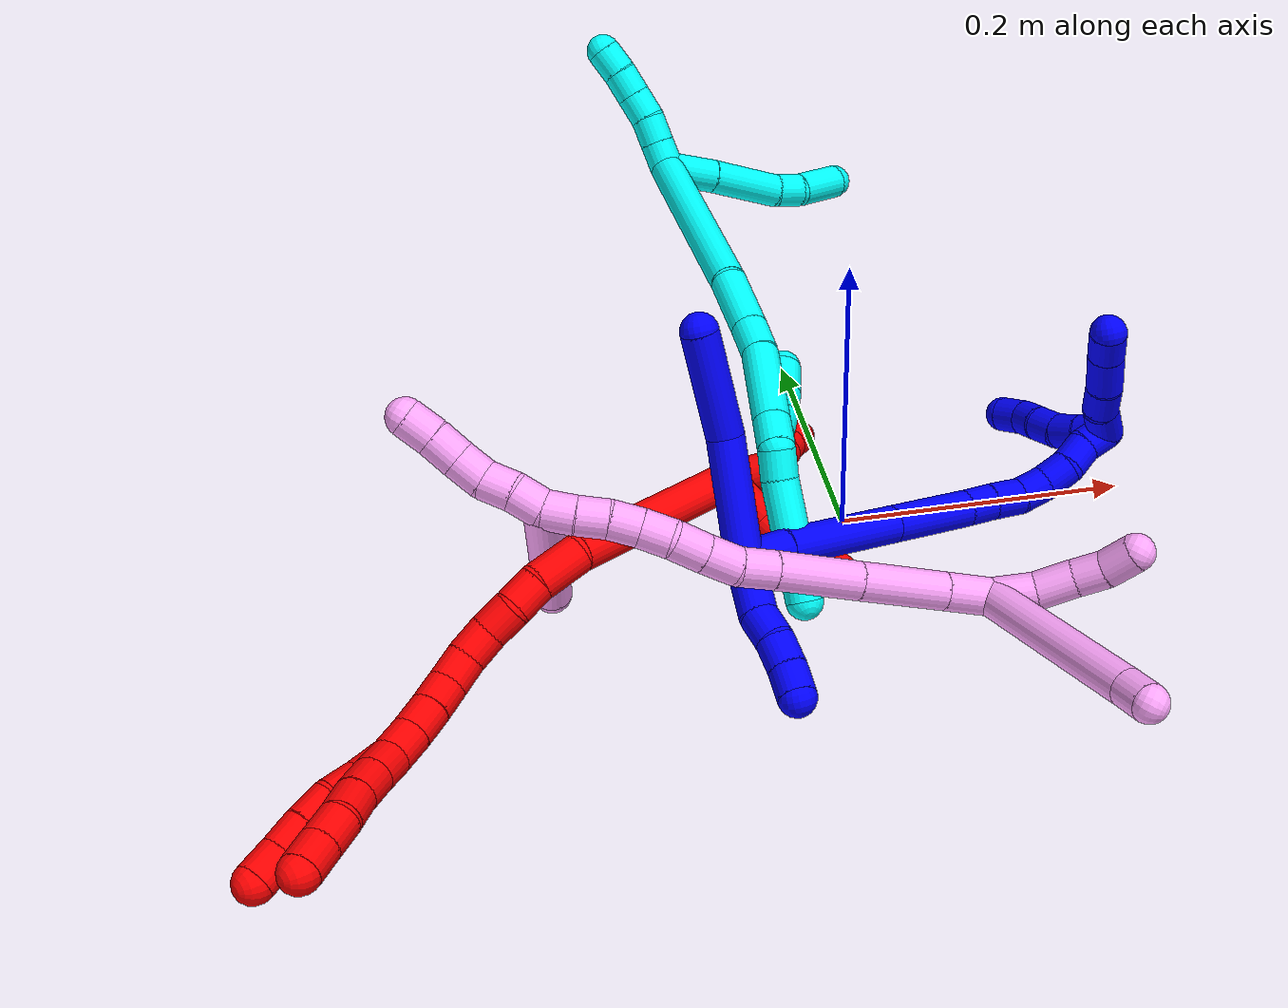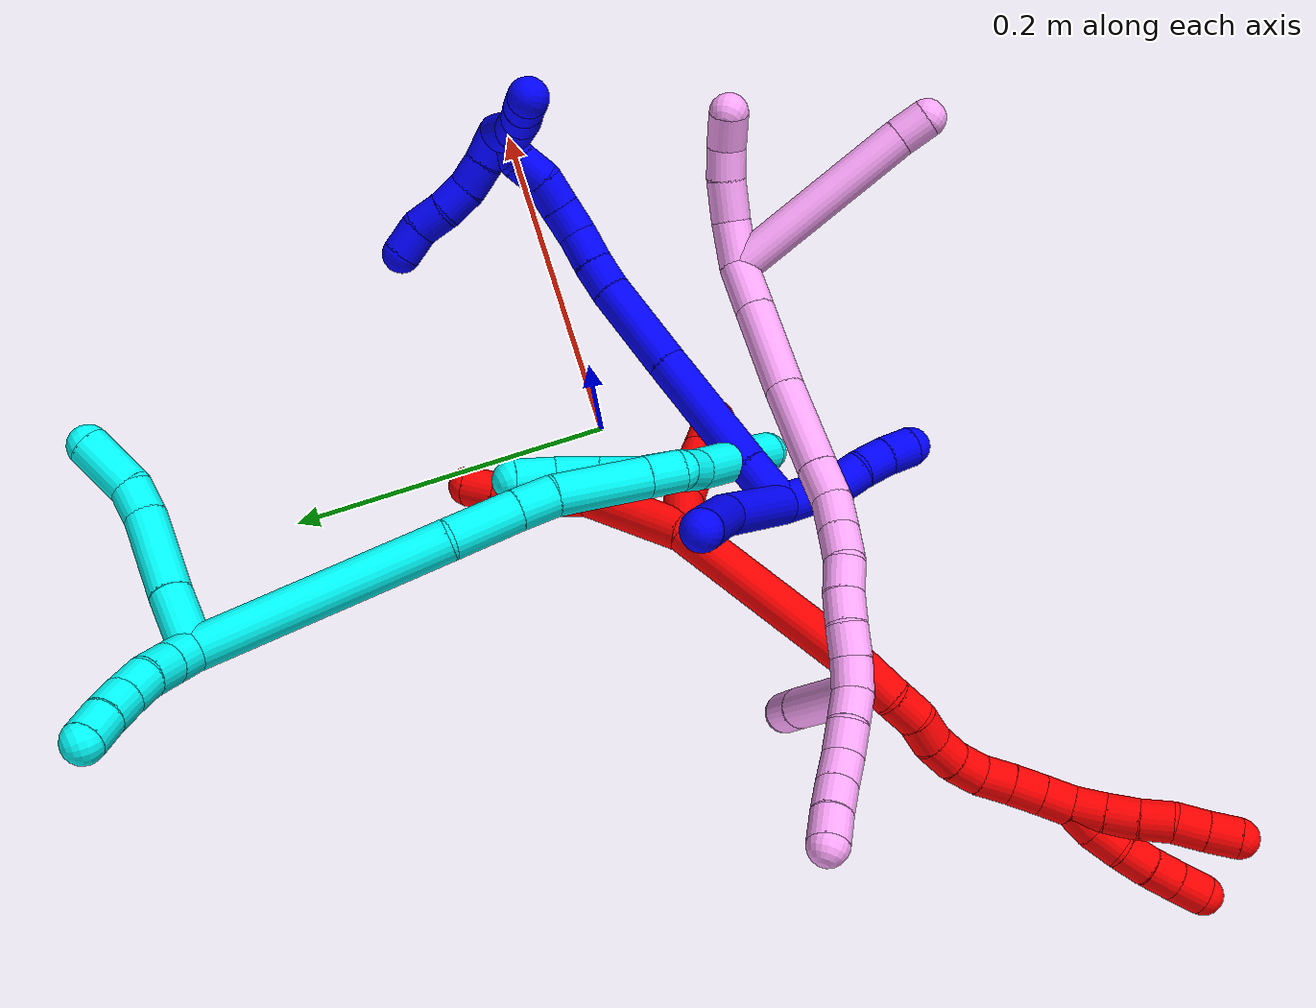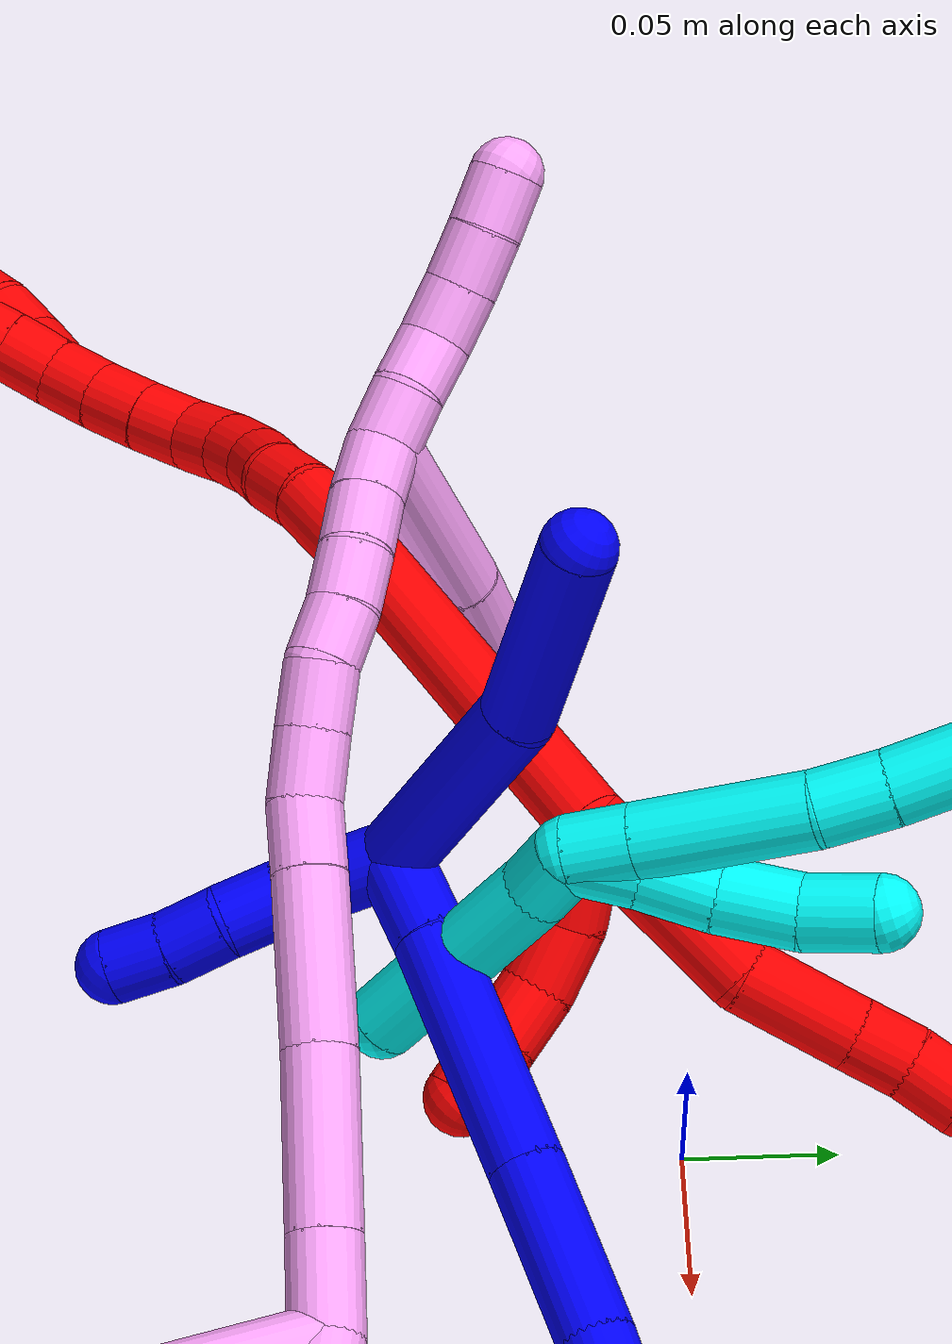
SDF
<sdf version="1.7">
 <world name="default">
  <plugin name="TubeGeneratorPlugin" filename="libtube_generator_plugin.so"/>
  <model name="photoneo_s_sensor">
   <static>1</static>
   <pose>0 0 2 1.57079 1.57079 3.14159</pose>
   <link name="link">
    <inertial><mass>0.1</mass></inertial>
    <sensor name="sensor" type="depth">
     <update_rate>30</update_rate>
     <camera>
      <horizontal_fov>1.22</horizontal_fov>
      <image><width>1920</width><height>1200</height><format>B8G8R8</format></image>
      <clip><near>0.1</near><far>4</far></clip>
      <depth_camera><output>points</output></depth_camera>
     </camera>
     <plugin name="camera_plugin" filename="libgazebo_ros_depth_camera.so">
      <baseline>0.2</baseline>
      <alwaysOn>1</alwaysOn>
      <updateRate>0.0</updateRate>
      <cameraName>camera_ir</cameraName>
      <imageTopicName>/camera/color/image_raw</imageTopicName>
      <cameraInfoTopicName>/camera/color/camera_info</cameraInfoTopicName>
      <depthImageTopicName>/camera/depth/image_raw</depthImageTopicName>
      <depthImageCameraInfoTopicName>/camera/depth/camera_info</depthImageCameraInfoTopicName>
      <pointCloudTopicName>/camera/depth/points</pointCloudTopicName>
      <frameName>fr_optical</frameName>
      <pointCloudCutoff>0.1</pointCloudCutoff>
      <pointCloudCutoffMax>2.0</pointCloudCutoffMax>
      <distortionK1>0</distortionK1>
      <distortionK2>0</distortionK2>
      <distortionK3>0</distortionK3>
      <distortionT1>0</distortionT1>
      <distortionT2>0</distortionT2>
      <CxPrime>0</CxPrime>
      <Cx>0</Cx>
      <Cy>0</Cy>
      <focalLength>0</focalLength>
      <hackBaseline>0</hackBaseline>
     </plugin>
    </sensor>
   </link>
  </model>
  <gravity>0 0 -9.8</gravity>
  <magnetic_field>6e-06 2.3e-05 -4.2e-05</magnetic_field>
  <atmosphere type="adiabatic"/>
  <physics name="default_physics" default="0" type="ode">
   <max_step_size>0.003</max_step_size>
   <real_time_factor>1</real_time_factor>
   <real_time_update_rate>1000</real_time_update_rate>
   <max_contacts>10000</max_contacts>
   <ode>
    <solver>
     <type>quick</type>
     <iters>100</iters>
     <sor>1.3</sor>
     <use_dynamic_moi_rescaling>0</use_dynamic_moi_rescaling>
    </solver>
    <constraints>
     <contact_max_correcting_vel>0</contact_max_correcting_vel>
     <contact_surface_layer>0.001</contact_surface_layer>
     <cfm>0</cfm>
     <erp>0.2</erp>
    </constraints>
   </ode>
  </physics>
  <scene><ambient>0.4 0.4 0.4 1</ambient><background>0.7 0.7 0.7 1</background><shadows>0</shadows></scene>
  <audio><device>default</device></audio>
  <spherical_coordinates>
   <surface_model>EARTH_WGS84</surface_model>
   <latitude_deg>0</latitude_deg>
   <longitude_deg>0</longitude_deg>
   <elevation>0</elevation>
   <heading_deg>0</heading_deg>
  </spherical_coordinates>
  <model name="bin">
   <static>1</static>
   <link name="bottom">
    <collision name="collision-bottom">
     <pose>0 0 -0.01 0 -0 0</pose>
     <geometry><box><size>0.8 0.6 0.02</size></box></geometry>
     <surface>
      <friction><ode><mu>100</mu><mu2>100</mu2></ode></friction>
      <contact><collide_bitmask>65535</collide_bitmask></contact>
     </surface>
    </collision>
   </link>
   <link name="west_wall">
    <collision name="collision-west_wall">
     <pose>-0.41 0 0.1 0 -0 0</pose>
     <geometry><box><size>0.02 0.6 0.2</size></box></geometry>
     <surface>
      <friction><ode><mu>100</mu><mu2>100</mu2></ode></friction>
      <contact><collide_bitmask>65535</collide_bitmask></contact>
     </surface>
    </collision>
   </link>
   <link name="east_wall">
    <collision name="collision-east_wall">
     <pose>0.41 0 0.1 0 -0 0</pose>
     <geometry><box><size>0.02 0.6 0.2</size></box></geometry>
     <surface>
      <friction><ode><mu>100</mu><mu2>100</mu2></ode></friction>
      <contact><collide_bitmask>65535</collide_bitmask></contact>
     </surface>
    </collision>
   </link>
   <link name="south_wall">
    <collision name="collision-south_wall">
     <pose>0 -0.31 0.1 0 -0 0</pose>
     <geometry><box><size>0.8 0.02 0.2</size></box></geometry>
     <surface>
      <friction><ode><mu>100</mu><mu2>100</mu2></ode></friction>
      <contact><collide_bitmask>65535</collide_bitmask></contact>
     </surface>
    </collision>
   </link>
   <link name="north_wall">
    <collision name="collision-north_wall">
     <pose>0 0.31 0.1 0 -0 0</pose>
     <geometry><box><size>0.8 0.02 0.2</size></box></geometry>
     <surface>
      <friction><ode><mu>100</mu><mu2>100</mu2></ode></friction>
      <contact><collide_bitmask>65535</collide_bitmask></contact>
     </surface>
    </collision>
   </link>
  </model>
  <model name="1">
   <static>0</static>
   <link name="1">
    <collision name="collision-cylinder-e_1_2_8">
     <pose>0.002319 -8.8e-05 0.03978 0.002206 0.058235 6.4e-05</pose>
     <geometry><cylinder><radius>0.0125</radius><length>0.079696</length></cylinder></geometry>
     <surface>
      <friction><ode><mu>1.16</mu><mu2>1.16</mu2><slip1>0</slip1><slip2>0</slip2></ode></friction>
      <contact><ode><kp>1e+06</kp><kd>1</kd><max_vel>0</max_vel><min_depth>0.001</min_depth></ode></contact>
     </surface>
    </collision>
    <visual name="visual-cylinder-e_1_2_8">
     <pose>0.002319 -8.8e-05 0.03978 0.002206 0.058235 6.4e-05</pose>
     <geometry><cylinder><radius>0.0125</radius><length>0.079696</length></cylinder></geometry>
     <material><ambient>0 0 1 1</ambient></material>
    </visual>
    <collision name="collision-cylinder-e_2_8_6">
     <pose>0.000359 -0.007727 0.113624 0.218161 -0.122052 -0.013383</pose>
     <geometry><cylinder><radius>0.0125</radius><length>0.070304</length></cylinder></geometry>
     <surface>
      <friction><ode><mu>1.16</mu><mu2>1.16</mu2><slip1>0</slip1><slip2>0</slip2></ode></friction>
      <contact><ode><kp>1e+06</kp><kd>1</kd><max_vel>0</max_vel><min_depth>0.001</min_depth></ode></contact>
     </surface>
    </collision>
    <visual name="visual-cylinder-e_2_8_6">
     <pose>0.000359 -0.007727 0.113624 0.218161 -0.122052 -0.013383</pose>
     <geometry><cylinder><radius>0.0125</radius><length>0.070304</length></cylinder></geometry>
     <material><ambient>0 0 1 1</ambient></material>
    </visual>
    <collision name="collision-cylinder-e_1_2_9">
     <pose>-0.003398 -0.010797 -0.015916 2.54556 -0.174898 -0.556062</pose>
     <geometry><cylinder><radius>0.0125</radius><length>0.039061</length></cylinder></geometry>
     <surface>
      <friction><ode><mu>1.16</mu><mu2>1.16</mu2><slip1>0</slip1><slip2>0</slip2></ode></friction>
      <contact><ode><kp>1e+06</kp><kd>1</kd><max_vel>0</max_vel><min_depth>0.001</min_depth></ode></contact>
     </surface>
    </collision>
    <visual name="visual-cylinder-e_1_2_9">
     <pose>-0.003398 -0.010797 -0.015916 2.54556 -0.174898 -0.556062</pose>
     <geometry><cylinder><radius>0.0125</radius><length>0.039061</length></cylinder></geometry>
     <material><ambient>0 0 1 1</ambient></material>
    </visual>
    <collision name="collision-cylinder-e_2_9_10">
     <pose>-0.006305 -0.029275 -0.038798 2.30729 0.047454 0.106999</pose>
     <geometry><cylinder><radius>0.0125</radius><length>0.020761</length></cylinder></geometry>
     <surface>
      <friction><ode><mu>1.16</mu><mu2>1.16</mu2><slip1>0</slip1><slip2>0</slip2></ode></friction>
      <contact><ode><kp>1e+06</kp><kd>1</kd><max_vel>0</max_vel><min_depth>0.001</min_depth></ode></contact>
     </surface>
    </collision>
    <visual name="visual-cylinder-e_2_9_10">
     <pose>-0.006305 -0.029275 -0.038798 2.30729 0.047454 0.106999</pose>
     <geometry><cylinder><radius>0.0125</radius><length>0.020761</length></cylinder></geometry>
     <material><ambient>0 0 1 1</ambient></material>
    </visual>
    <collision name="collision-cylinder-e_3_10_11">
     <pose>-0.006066 -0.042999 -0.053815 2.49789 -0.025173 -0.07546</pose>
     <geometry><cylinder><radius>0.0125</radius><length>0.020142</length></cylinder></geometry>
     <surface>
      <friction><ode><mu>1.16</mu><mu2>1.16</mu2><slip1>0</slip1><slip2>0</slip2></ode></friction>
      <contact><ode><kp>1e+06</kp><kd>1</kd><max_vel>0</max_vel><min_depth>0.001</min_depth></ode></contact>
     </surface>
    </collision>
    <visual name="visual-cylinder-e_3_10_11">
     <pose>-0.006066 -0.042999 -0.053815 2.49789 -0.025173 -0.07546</pose>
     <geometry><cylinder><radius>0.0125</radius><length>0.020142</length></cylinder></geometry>
     <material><ambient>0 0 1 1</ambient></material>
    </visual>
    <collision name="collision-cylinder-e_4_11_5">
     <pose>-0.007757 -0.055417 -0.06946 2.44298 -0.143996 -0.390956</pose>
     <geometry><cylinder><radius>0.0125</radius><length>0.020036</length></cylinder></geometry>
     <surface>
      <friction><ode><mu>1.16</mu><mu2>1.16</mu2><slip1>0</slip1><slip2>0</slip2></ode></friction>
      <contact><ode><kp>1e+06</kp><kd>1</kd><max_vel>0</max_vel><min_depth>0.001</min_depth></ode></contact>
     </surface>
    </collision>
    <visual name="visual-cylinder-e_4_11_5">
     <pose>-0.007757 -0.055417 -0.06946 2.44298 -0.143996 -0.390956</pose>
     <geometry><cylinder><radius>0.0125</radius><length>0.020036</length></cylinder></geometry>
     <material><ambient>0 0 1 1</ambient></material>
    </visual>
    <collision name="collision-cylinder-e_1_2_12">
     <pose>0.016016 0.001963 -0.000158 -1.65098 1.44847 -1.52844</pose>
     <geometry><cylinder><radius>0.0125</radius><length>0.032273</length></cylinder></geometry>
     <surface>
      <friction><ode><mu>1.16</mu><mu2>1.16</mu2><slip1>0</slip1><slip2>0</slip2></ode></friction>
      <contact><ode><kp>1e+06</kp><kd>1</kd><max_vel>0</max_vel><min_depth>0.001</min_depth></ode></contact>
     </surface>
    </collision>
    <visual name="visual-cylinder-e_1_2_12">
     <pose>0.016016 0.001963 -0.000158 -1.65098 1.44847 -1.52844</pose>
     <geometry><cylinder><radius>0.0125</radius><length>0.032273</length></cylinder></geometry>
     <material><ambient>0 0 1 1</ambient></material>
    </visual>
    <collision name="collision-cylinder-e_2_12_13">
     <pose>0.073174 0.009221 -0.003764 -2.14803 1.41838 -2.0147</pose>
     <geometry><cylinder><radius>0.0125</radius><length>0.083249</length></cylinder></geometry>
     <surface>
      <friction><ode><mu>1.16</mu><mu2>1.16</mu2><slip1>0</slip1><slip2>0</slip2></ode></friction>
      <contact><ode><kp>1e+06</kp><kd>1</kd><max_vel>0</max_vel><min_depth>0.001</min_depth></ode></contact>
     </surface>
    </collision>
    <visual name="visual-cylinder-e_2_12_13">
     <pose>0.073174 0.009221 -0.003764 -2.14803 1.41838 -2.0147</pose>
     <geometry><cylinder><radius>0.0125</radius><length>0.083249</length></cylinder></geometry>
     <material><ambient>0 0 1 1</ambient></material>
    </visual>
    <collision name="collision-cylinder-e_3_13_14">
     <pose>0.144218 0.018027 -0.009704 -2.18801 1.42785 -2.06634</pose>
     <geometry><cylinder><radius>0.0125</radius><length>0.060421</length></cylinder></geometry>
     <surface>
      <friction><ode><mu>1.16</mu><mu2>1.16</mu2><slip1>0</slip1><slip2>0</slip2></ode></friction>
      <contact><ode><kp>1e+06</kp><kd>1</kd><max_vel>0</max_vel><min_depth>0.001</min_depth></ode></contact>
     </surface>
    </collision>
    <visual name="visual-cylinder-e_3_13_14">
     <pose>0.144218 0.018027 -0.009704 -2.18801 1.42785 -2.06634</pose>
     <geometry><cylinder><radius>0.0125</radius><length>0.060421</length></cylinder></geometry>
     <material><ambient>0 0 1 1</ambient></material>
    </visual>
    <collision name="collision-cylinder-e_4_14_15">
     <pose>0.184485 0.02161 -0.012508 -2.91135 1.53972 -2.90415</pose>
     <geometry><cylinder><radius>0.0125</radius><length>0.02074</length></cylinder></geometry>
     <surface>
      <friction><ode><mu>1.16</mu><mu2>1.16</mu2><slip1>0</slip1><slip2>0</slip2></ode></friction>
      <contact><ode><kp>1e+06</kp><kd>1</kd><max_vel>0</max_vel><min_depth>0.001</min_depth></ode></contact>
     </surface>
    </collision>
    <visual name="visual-cylinder-e_4_14_15">
     <pose>0.184485 0.02161 -0.012508 -2.91135 1.53972 -2.90415</pose>
     <geometry><cylinder><radius>0.0125</radius><length>0.02074</length></cylinder></geometry>
     <material><ambient>0 0 1 1</ambient></material>
    </visual>
    <collision name="collision-cylinder-e_5_15_16">
     <pose>0.205963 0.021018 -0.013606 2.43787 1.47857 2.37599</pose>
     <geometry><cylinder><radius>0.0125</radius><length>0.02232</length></cylinder></geometry>
     <surface>
      <friction><ode><mu>1.16</mu><mu2>1.16</mu2><slip1>0</slip1><slip2>0</slip2></ode></friction>
      <contact><ode><kp>1e+06</kp><kd>1</kd><max_vel>0</max_vel><min_depth>0.001</min_depth></ode></contact>
     </surface>
    </collision>
    <visual name="visual-cylinder-e_5_15_16">
     <pose>0.205963 0.021018 -0.013606 2.43787 1.47857 2.37599</pose>
     <geometry><cylinder><radius>0.0125</radius><length>0.02232</length></cylinder></geometry>
     <material><ambient>0 0 1 1</ambient></material>
    </visual>
    <collision name="collision-cylinder-e_6_16_17">
     <pose>0.227008 0.01929 -0.012257 0.462486 1.33535 0.36712</pose>
     <geometry><cylinder><radius>0.0125</radius><length>0.020429</length></cylinder></geometry>
     <surface>
      <friction><ode><mu>1.16</mu><mu2>1.16</mu2><slip1>0</slip1><slip2>0</slip2></ode></friction>
      <contact><ode><kp>1e+06</kp><kd>1</kd><max_vel>0</max_vel><min_depth>0.001</min_depth></ode></contact>
     </surface>
    </collision>
    <visual name="visual-cylinder-e_6_16_17">
     <pose>0.227008 0.01929 -0.012257 0.462486 1.33535 0.36712</pose>
     <geometry><cylinder><radius>0.0125</radius><length>0.020429</length></cylinder></geometry>
     <material><ambient>0 0 1 1</ambient></material>
    </visual>
    <collision name="collision-cylinder-e_7_17_18">
     <pose>0.246226 0.016309 -0.006389 0.474377 1.14609 0.309479</pose>
     <geometry><cylinder><radius>0.0125</radius><length>0.020382</length></cylinder></geometry>
     <surface>
      <friction><ode><mu>1.16</mu><mu2>1.16</mu2><slip1>0</slip1><slip2>0</slip2></ode></friction>
      <contact><ode><kp>1e+06</kp><kd>1</kd><max_vel>0</max_vel><min_depth>0.001</min_depth></ode></contact>
     </surface>
    </collision>
    <visual name="visual-cylinder-e_7_17_18">
     <pose>0.246226 0.016309 -0.006389 0.474377 1.14609 0.309479</pose>
     <geometry><cylinder><radius>0.0125</radius><length>0.020382</length></cylinder></geometry>
     <material><ambient>0 0 1 1</ambient></material>
    </visual>
    <collision name="collision-cylinder-e_8_18_19">
     <pose>0.264058 0.015448 0.0025 -0.202314 1.01903 -0.113303</pose>
     <geometry><cylinder><radius>0.0125</radius><length>0.020072</length></cylinder></geometry>
     <surface>
      <friction><ode><mu>1.16</mu><mu2>1.16</mu2><slip1>0</slip1><slip2>0</slip2></ode></friction>
      <contact><ode><kp>1e+06</kp><kd>1</kd><max_vel>0</max_vel><min_depth>0.001</min_depth></ode></contact>
     </surface>
    </collision>
    <visual name="visual-cylinder-e_8_18_19">
     <pose>0.264058 0.015448 0.0025 -0.202314 1.01903 -0.113303</pose>
     <geometry><cylinder><radius>0.0125</radius><length>0.020072</length></cylinder></geometry>
     <material><ambient>0 0 1 1</ambient></material>
    </visual>
    <collision name="collision-cylinder-e_9_19_1">
     <pose>0.282171 0.015831 0.010683 0.218854 1.25713 0.159388</pose>
     <geometry><cylinder><radius>0.0125</radius><length>0.020115</length></cylinder></geometry>
     <surface>
      <friction><ode><mu>1.16</mu><mu2>1.16</mu2><slip1>0</slip1><slip2>0</slip2></ode></friction>
      <contact><ode><kp>1e+06</kp><kd>1</kd><max_vel>0</max_vel><min_depth>0.001</min_depth></ode></contact>
     </surface>
    </collision>
    <visual name="visual-cylinder-e_9_19_1">
     <pose>0.282171 0.015831 0.010683 0.218854 1.25713 0.159388</pose>
     <geometry><cylinder><radius>0.0125</radius><length>0.020115</length></cylinder></geometry>
     <material><ambient>0 0 1 1</ambient></material>
    </visual>
    <collision name="collision-cylinder-e_1_1_20">
     <pose>0.287623 0.024256 0.014251 -1.51167 -0.424094 0.400398</pose>
     <geometry><cylinder><radius>0.0125</radius><length>0.02</length></cylinder></geometry>
     <surface>
      <friction><ode><mu>1.16</mu><mu2>1.16</mu2><slip1>0</slip1><slip2>0</slip2></ode></friction>
      <contact><ode><kp>1e+06</kp><kd>1</kd><max_vel>0</max_vel><min_depth>0.001</min_depth></ode></contact>
     </surface>
    </collision>
    <visual name="visual-cylinder-e_1_1_20">
     <pose>0.287623 0.024256 0.014251 -1.51167 -0.424094 0.400398</pose>
     <geometry><cylinder><radius>0.0125</radius><length>0.02</length></cylinder></geometry>
     <material><ambient>0 0 1 1</ambient></material>
    </visual>
    <collision name="collision-cylinder-e_2_20_21">
     <pose>0.280484 0.042853 0.015576 -1.48813 -0.307214 0.28315</pose>
     <geometry><cylinder><radius>0.0125</radius><length>0.02</length></cylinder></geometry>
     <surface>
      <friction><ode><mu>1.16</mu><mu2>1.16</mu2><slip1>0</slip1><slip2>0</slip2></ode></friction>
      <contact><ode><kp>1e+06</kp><kd>1</kd><max_vel>0</max_vel><min_depth>0.001</min_depth></ode></contact>
     </surface>
    </collision>
    <visual name="visual-cylinder-e_2_20_21">
     <pose>0.280484 0.042853 0.015576 -1.48813 -0.307214 0.28315</pose>
     <geometry><cylinder><radius>0.0125</radius><length>0.02</length></cylinder></geometry>
     <material><ambient>0 0 1 1</ambient></material>
    </visual>
    <collision name="collision-cylinder-e_3_21_22">
     <pose>0.27605 0.061811 0.019287 -1.27105 -0.141436 0.104404</pose>
     <geometry><cylinder><radius>0.0125</radius><length>0.02</length></cylinder></geometry>
     <surface>
      <friction><ode><mu>1.16</mu><mu2>1.16</mu2><slip1>0</slip1><slip2>0</slip2></ode></friction>
      <contact><ode><kp>1e+06</kp><kd>1</kd><max_vel>0</max_vel><min_depth>0.001</min_depth></ode></contact>
     </surface>
    </collision>
    <visual name="visual-cylinder-e_3_21_22">
     <pose>0.27605 0.061811 0.019287 -1.27105 -0.141436 0.104404</pose>
     <geometry><cylinder><radius>0.0125</radius><length>0.02</length></cylinder></geometry>
     <material><ambient>0 0 1 1</ambient></material>
    </visual>
    <collision name="collision-cylinder-e_4_22_23">
     <pose>0.274975 0.081054 0.024248 -1.36546 0.033383 -0.027147</pose>
     <geometry><cylinder><radius>0.0125</radius><length>0.02</length></cylinder></geometry>
     <surface>
      <friction><ode><mu>1.16</mu><mu2>1.16</mu2><slip1>0</slip1><slip2>0</slip2></ode></friction>
      <contact><ode><kp>1e+06</kp><kd>1</kd><max_vel>0</max_vel><min_depth>0.001</min_depth></ode></contact>
     </surface>
    </collision>
    <visual name="visual-cylinder-e_4_22_23">
     <pose>0.274975 0.081054 0.024248 -1.36546 0.033383 -0.027147</pose>
     <geometry><cylinder><radius>0.0125</radius><length>0.02</length></cylinder></geometry>
     <material><ambient>0 0 1 1</ambient></material>
    </visual>
    <collision name="collision-cylinder-e_5_23_4">
     <pose>0.272209 0.100162 0.028148 -1.37369 -0.315107 0.259101</pose>
     <geometry><cylinder><radius>0.0125</radius><length>0.02</length></cylinder></geometry>
     <surface>
      <friction><ode><mu>1.16</mu><mu2>1.16</mu2><slip1>0</slip1><slip2>0</slip2></ode></friction>
      <contact><ode><kp>1e+06</kp><kd>1</kd><max_vel>0</max_vel><min_depth>0.001</min_depth></ode></contact>
     </surface>
    </collision>
    <visual name="visual-cylinder-e_5_23_4">
     <pose>0.272209 0.100162 0.028148 -1.37369 -0.315107 0.259101</pose>
     <geometry><cylinder><radius>0.0125</radius><length>0.02</length></cylinder></geometry>
     <material><ambient>0 0 1 1</ambient></material>
    </visual>
    <collision name="collision-cylinder-e_1_1_24">
     <pose>0.285286 0.005556 0.023591 0.771158 -0.438015 -0.180197</pose>
     <geometry><cylinder><radius>0.0125</radius><length>0.030424</length></cylinder></geometry>
     <surface>
      <friction><ode><mu>1.16</mu><mu2>1.16</mu2><slip1>0</slip1><slip2>0</slip2></ode></friction>
      <contact><ode><kp>1e+06</kp><kd>1</kd><max_vel>0</max_vel><min_depth>0.001</min_depth></ode></contact>
     </surface>
    </collision>
    <visual name="visual-cylinder-e_1_1_24">
     <pose>0.285286 0.005556 0.023591 0.771158 -0.438015 -0.180197</pose>
     <geometry><cylinder><radius>0.0125</radius><length>0.030424</length></cylinder></geometry>
     <material><ambient>0 0 1 1</ambient></material>
    </visual>
    <collision name="collision-cylinder-e_2_24_25">
     <pose>0.277043 -0.011485 0.041491 0.747765 -0.162248 -0.063774</pose>
     <geometry><cylinder><radius>0.0125</radius><length>0.022172</length></cylinder></geometry>
     <surface>
      <friction><ode><mu>1.16</mu><mu2>1.16</mu2><slip1>0</slip1><slip2>0</slip2></ode></friction>
      <contact><ode><kp>1e+06</kp><kd>1</kd><max_vel>0</max_vel><min_depth>0.001</min_depth></ode></contact>
     </surface>
    </collision>
    <visual name="visual-cylinder-e_2_24_25">
     <pose>0.277043 -0.011485 0.041491 0.747765 -0.162248 -0.063774</pose>
     <geometry><cylinder><radius>0.0125</radius><length>0.022172</length></cylinder></geometry>
     <material><ambient>0 0 1 1</ambient></material>
    </visual>
    <collision name="collision-cylinder-e_3_25_26">
     <pose>0.273162 -0.026475 0.060692 0.594015 -0.153727 -0.047134</pose>
     <geometry><cylinder><radius>0.0125</radius><length>0.027303</length></cylinder></geometry>
     <surface>
      <friction><ode><mu>1.16</mu><mu2>1.16</mu2><slip1>0</slip1><slip2>0</slip2></ode></friction>
      <contact><ode><kp>1e+06</kp><kd>1</kd><max_vel>0</max_vel><min_depth>0.001</min_depth></ode></contact>
     </surface>
    </collision>
    <visual name="visual-cylinder-e_3_25_26">
     <pose>0.273162 -0.026475 0.060692 0.594015 -0.153727 -0.047134</pose>
     <geometry><cylinder><radius>0.0125</radius><length>0.027303</length></cylinder></geometry>
     <material><ambient>0 0 1 1</ambient></material>
    </visual>
    <collision name="collision-cylinder-e_4_26_3">
     <pose>0.269456 -0.040094 0.079718 0.658344 -0.161475 -0.055266</pose>
     <geometry><cylinder><radius>0.0125</radius><length>0.020102</length></cylinder></geometry>
     <surface>
      <friction><ode><mu>1.16</mu><mu2>1.16</mu2><slip1>0</slip1><slip2>0</slip2></ode></friction>
      <contact><ode><kp>1e+06</kp><kd>1</kd><max_vel>0</max_vel><min_depth>0.001</min_depth></ode></contact>
     </surface>
    </collision>
    <visual name="visual-cylinder-e_4_26_3">
     <pose>0.269456 -0.040094 0.079718 0.658344 -0.161475 -0.055266</pose>
     <geometry><cylinder><radius>0.0125</radius><length>0.020102</length></cylinder></geometry>
     <material><ambient>0 0 1 1</ambient></material>
    </visual>
    <collision name="collision-sphere-3">
     <pose>0.26784 -0.046163 0.087565 0 -0 0</pose>
     <geometry><sphere><radius>0.0125</radius></sphere></geometry>
     <surface>
      <friction><ode><mu>1.16</mu><mu2>1.16</mu2><slip1>0</slip1><slip2>0</slip2></ode></friction>
      <contact><ode><kp>1e+06</kp><kd>1</kd><max_vel>0</max_vel><min_depth>0.001</min_depth></ode></contact>
     </surface>
    </collision>
    <visual name="visual-sphere-3">
     <pose>0.26784 -0.046163 0.087565 0 -0 0</pose>
     <geometry><sphere><radius>0.0125</radius></sphere></geometry>
     <material><ambient>0 0 1 1</ambient></material>
    </visual>
    <collision name="collision-sphere-26">
     <pose>0.271072 -0.034025 0.071871 0 -0 0</pose>
     <geometry><sphere><radius>0.0125</radius></sphere></geometry>
     <surface>
      <friction><ode><mu>1.16</mu><mu2>1.16</mu2><slip1>0</slip1><slip2>0</slip2></ode></friction>
      <contact><ode><kp>1e+06</kp><kd>1</kd><max_vel>0</max_vel><min_depth>0.001</min_depth></ode></contact>
     </surface>
    </collision>
    <visual name="visual-sphere-26">
     <pose>0.271072 -0.034025 0.071871 0 -0 0</pose>
     <geometry><sphere><radius>0.0125</radius></sphere></geometry>
     <material><ambient>0 0 1 1</ambient></material>
    </visual>
    <collision name="collision-sphere-25">
     <pose>0.275252 -0.018924 0.049513 0 -0 0</pose>
     <geometry><sphere><radius>0.0125</radius></sphere></geometry>
     <surface>
      <friction><ode><mu>1.16</mu><mu2>1.16</mu2><slip1>0</slip1><slip2>0</slip2></ode></friction>
      <contact><ode><kp>1e+06</kp><kd>1</kd><max_vel>0</max_vel><min_depth>0.001</min_depth></ode></contact>
     </surface>
    </collision>
    <visual name="visual-sphere-25">
     <pose>0.275252 -0.018924 0.049513 0 -0 0</pose>
     <geometry><sphere><radius>0.0125</radius></sphere></geometry>
     <material><ambient>0 0 1 1</ambient></material>
    </visual>
    <collision name="collision-sphere-24">
     <pose>0.278834 -0.004045 0.03347 0 -0 0</pose>
     <geometry><sphere><radius>0.0125</radius></sphere></geometry>
     <surface>
      <friction><ode><mu>1.16</mu><mu2>1.16</mu2><slip1>0</slip1><slip2>0</slip2></ode></friction>
      <contact><ode><kp>1e+06</kp><kd>1</kd><max_vel>0</max_vel><min_depth>0.001</min_depth></ode></contact>
     </surface>
    </collision>
    <visual name="visual-sphere-24">
     <pose>0.278834 -0.004045 0.03347 0 -0 0</pose>
     <geometry><sphere><radius>0.0125</radius></sphere></geometry>
     <material><ambient>0 0 1 1</ambient></material>
    </visual>
    <collision name="collision-sphere-4">
     <pose>0.26911 0.109486 0.03001 0 -0 0</pose>
     <geometry><sphere><radius>0.0125</radius></sphere></geometry>
     <surface>
      <friction><ode><mu>1.16</mu><mu2>1.16</mu2><slip1>0</slip1><slip2>0</slip2></ode></friction>
      <contact><ode><kp>1e+06</kp><kd>1</kd><max_vel>0</max_vel><min_depth>0.001</min_depth></ode></contact>
     </surface>
    </collision>
    <visual name="visual-sphere-4">
     <pose>0.26911 0.109486 0.03001 0 -0 0</pose>
     <geometry><sphere><radius>0.0125</radius></sphere></geometry>
     <material><ambient>0 0 1 1</ambient></material>
    </visual>
    <collision name="collision-sphere-23">
     <pose>0.275308 0.090839 0.026286 0 -0 0</pose>
     <geometry><sphere><radius>0.0125</radius></sphere></geometry>
     <surface>
      <friction><ode><mu>1.16</mu><mu2>1.16</mu2><slip1>0</slip1><slip2>0</slip2></ode></friction>
      <contact><ode><kp>1e+06</kp><kd>1</kd><max_vel>0</max_vel><min_depth>0.001</min_depth></ode></contact>
     </surface>
    </collision>
    <visual name="visual-sphere-23">
     <pose>0.275308 0.090839 0.026286 0 -0 0</pose>
     <geometry><sphere><radius>0.0125</radius></sphere></geometry>
     <material><ambient>0 0 1 1</ambient></material>
    </visual>
    <collision name="collision-sphere-22">
     <pose>0.274641 0.07127 0.02221 0 -0 0</pose>
     <geometry><sphere><radius>0.0125</radius></sphere></geometry>
     <surface>
      <friction><ode><mu>1.16</mu><mu2>1.16</mu2><slip1>0</slip1><slip2>0</slip2></ode></friction>
      <contact><ode><kp>1e+06</kp><kd>1</kd><max_vel>0</max_vel><min_depth>0.001</min_depth></ode></contact>
     </surface>
    </collision>
    <visual name="visual-sphere-22">
     <pose>0.274641 0.07127 0.02221 0 -0 0</pose>
     <geometry><sphere><radius>0.0125</radius></sphere></geometry>
     <material><ambient>0 0 1 1</ambient></material>
    </visual>
    <collision name="collision-sphere-21">
     <pose>0.27746 0.052352 0.016363 0 -0 0</pose>
     <geometry><sphere><radius>0.0125</radius></sphere></geometry>
     <surface>
      <friction><ode><mu>1.16</mu><mu2>1.16</mu2><slip1>0</slip1><slip2>0</slip2></ode></friction>
      <contact><ode><kp>1e+06</kp><kd>1</kd><max_vel>0</max_vel><min_depth>0.001</min_depth></ode></contact>
     </surface>
    </collision>
    <visual name="visual-sphere-21">
     <pose>0.27746 0.052352 0.016363 0 -0 0</pose>
     <geometry><sphere><radius>0.0125</radius></sphere></geometry>
     <material><ambient>0 0 1 1</ambient></material>
    </visual>
    <collision name="collision-sphere-20">
     <pose>0.283508 0.033354 0.014789 0 -0 0</pose>
     <geometry><sphere><radius>0.0125</radius></sphere></geometry>
     <surface>
      <friction><ode><mu>1.16</mu><mu2>1.16</mu2><slip1>0</slip1><slip2>0</slip2></ode></friction>
      <contact><ode><kp>1e+06</kp><kd>1</kd><max_vel>0</max_vel><min_depth>0.001</min_depth></ode></contact>
     </surface>
    </collision>
    <visual name="visual-sphere-20">
     <pose>0.283508 0.033354 0.014789 0 -0 0</pose>
     <geometry><sphere><radius>0.0125</radius></sphere></geometry>
     <material><ambient>0 0 1 1</ambient></material>
    </visual>
    <collision name="collision-sphere-11">
     <pose>-0.006319 -0.049041 -0.061868 0 -0 0</pose>
     <geometry><sphere><radius>0.0125</radius></sphere></geometry>
     <surface>
      <friction><ode><mu>1.16</mu><mu2>1.16</mu2><slip1>0</slip1><slip2>0</slip2></ode></friction>
      <contact><ode><kp>1e+06</kp><kd>1</kd><max_vel>0</max_vel><min_depth>0.001</min_depth></ode></contact>
     </surface>
    </collision>
    <visual name="visual-sphere-11">
     <pose>-0.006319 -0.049041 -0.061868 0 -0 0</pose>
     <geometry><sphere><radius>0.0125</radius></sphere></geometry>
     <material><ambient>0 0 1 1</ambient></material>
    </visual>
    <collision name="collision-sphere-10">
     <pose>-0.005812 -0.036956 -0.045762 0 -0 0</pose>
     <geometry><sphere><radius>0.0125</radius></sphere></geometry>
     <surface>
      <friction><ode><mu>1.16</mu><mu2>1.16</mu2><slip1>0</slip1><slip2>0</slip2></ode></friction>
      <contact><ode><kp>1e+06</kp><kd>1</kd><max_vel>0</max_vel><min_depth>0.001</min_depth></ode></contact>
     </surface>
    </collision>
    <visual name="visual-sphere-10">
     <pose>-0.005812 -0.036956 -0.045762 0 -0 0</pose>
     <geometry><sphere><radius>0.0125</radius></sphere></geometry>
     <material><ambient>0 0 1 1</ambient></material>
    </visual>
    <collision name="collision-sphere-6">
     <pose>-0.003921 -0.015279 0.147688 0 -0 0</pose>
     <geometry><sphere><radius>0.0125</radius></sphere></geometry>
     <surface>
      <friction><ode><mu>1.16</mu><mu2>1.16</mu2><slip1>0</slip1><slip2>0</slip2></ode></friction>
      <contact><ode><kp>1e+06</kp><kd>1</kd><max_vel>0</max_vel><min_depth>0.001</min_depth></ode></contact>
     </surface>
    </collision>
    <visual name="visual-sphere-6">
     <pose>-0.003921 -0.015279 0.147688 0 -0 0</pose>
     <geometry><sphere><radius>0.0125</radius></sphere></geometry>
     <material><ambient>0 0 1 1</ambient></material>
    </visual>
    <collision name="collision-sphere-9">
     <pose>-0.006797 -0.021593 -0.031833 0 -0 0</pose>
     <geometry><sphere><radius>0.0125</radius></sphere></geometry>
     <surface>
      <friction><ode><mu>1.16</mu><mu2>1.16</mu2><slip1>0</slip1><slip2>0</slip2></ode></friction>
      <contact><ode><kp>1e+06</kp><kd>1</kd><max_vel>0</max_vel><min_depth>0.001</min_depth></ode></contact>
     </surface>
    </collision>
    <visual name="visual-sphere-9">
     <pose>-0.006797 -0.021593 -0.031833 0 -0 0</pose>
     <geometry><sphere><radius>0.0125</radius></sphere></geometry>
     <material><ambient>0 0 1 1</ambient></material>
    </visual>
    <collision name="collision-sphere-2">
     <geometry><sphere><radius>0.0125</radius></sphere></geometry>
     <surface>
      <friction><ode><mu>1.16</mu><mu2>1.16</mu2><slip1>0</slip1><slip2>0</slip2></ode></friction>
      <contact><ode><kp>1e+06</kp><kd>1</kd><max_vel>0</max_vel><min_depth>0.001</min_depth></ode></contact>
     </surface>
    </collision>
    <visual name="visual-sphere-2">
     <geometry><sphere><radius>0.0125</radius></sphere></geometry>
     <material><ambient>0 0 1 1</ambient></material>
    </visual>
    <collision name="collision-sphere-19">
     <pose>0.272605 0.016505 0.007654 0 -0 0</pose>
     <geometry><sphere><radius>0.0125</radius></sphere></geometry>
     <surface>
      <friction><ode><mu>1.16</mu><mu2>1.16</mu2><slip1>0</slip1><slip2>0</slip2></ode></friction>
      <contact><ode><kp>1e+06</kp><kd>1</kd><max_vel>0</max_vel><min_depth>0.001</min_depth></ode></contact>
     </surface>
    </collision>
    <visual name="visual-sphere-19">
     <pose>0.272605 0.016505 0.007654 0 -0 0</pose>
     <geometry><sphere><radius>0.0125</radius></sphere></geometry>
     <material><ambient>0 0 1 1</ambient></material>
    </visual>
    <collision name="collision-sphere-8">
     <pose>0.004638 -0.000176 0.079561 0 -0 0</pose>
     <geometry><sphere><radius>0.0125</radius></sphere></geometry>
     <surface>
      <friction><ode><mu>1.16</mu><mu2>1.16</mu2><slip1>0</slip1><slip2>0</slip2></ode></friction>
      <contact><ode><kp>1e+06</kp><kd>1</kd><max_vel>0</max_vel><min_depth>0.001</min_depth></ode></contact>
     </surface>
    </collision>
    <visual name="visual-sphere-8">
     <pose>0.004638 -0.000176 0.079561 0 -0 0</pose>
     <geometry><sphere><radius>0.0125</radius></sphere></geometry>
     <material><ambient>0 0 1 1</ambient></material>
    </visual>
    <collision name="collision-sphere-5">
     <pose>-0.009194 -0.061794 -0.077051 0 -0 0</pose>
     <geometry><sphere><radius>0.0125</radius></sphere></geometry>
     <surface>
      <friction><ode><mu>1.16</mu><mu2>1.16</mu2><slip1>0</slip1><slip2>0</slip2></ode></friction>
      <contact><ode><kp>1e+06</kp><kd>1</kd><max_vel>0</max_vel><min_depth>0.001</min_depth></ode></contact>
     </surface>
    </collision>
    <visual name="visual-sphere-5">
     <pose>-0.009194 -0.061794 -0.077051 0 -0 0</pose>
     <geometry><sphere><radius>0.0125</radius></sphere></geometry>
     <material><ambient>0 0 1 1</ambient></material>
    </visual>
    <collision name="collision-sphere-12">
     <pose>0.032032 0.003925 -0.000315 0 -0 0</pose>
     <geometry><sphere><radius>0.0125</radius></sphere></geometry>
     <surface>
      <friction><ode><mu>1.16</mu><mu2>1.16</mu2><slip1>0</slip1><slip2>0</slip2></ode></friction>
      <contact><ode><kp>1e+06</kp><kd>1</kd><max_vel>0</max_vel><min_depth>0.001</min_depth></ode></contact>
     </surface>
    </collision>
    <visual name="visual-sphere-12">
     <pose>0.032032 0.003925 -0.000315 0 -0 0</pose>
     <geometry><sphere><radius>0.0125</radius></sphere></geometry>
     <material><ambient>0 0 1 1</ambient></material>
    </visual>
    <collision name="collision-sphere-13">
     <pose>0.114316 0.014517 -0.007213 0 -0 0</pose>
     <geometry><sphere><radius>0.0125</radius></sphere></geometry>
     <surface>
      <friction><ode><mu>1.16</mu><mu2>1.16</mu2><slip1>0</slip1><slip2>0</slip2></ode></friction>
      <contact><ode><kp>1e+06</kp><kd>1</kd><max_vel>0</max_vel><min_depth>0.001</min_depth></ode></contact>
     </surface>
    </collision>
    <visual name="visual-sphere-13">
     <pose>0.114316 0.014517 -0.007213 0 -0 0</pose>
     <geometry><sphere><radius>0.0125</radius></sphere></geometry>
     <material><ambient>0 0 1 1</ambient></material>
    </visual>
    <collision name="collision-sphere-14">
     <pose>0.17412 0.021536 -0.012195 0 -0 0</pose>
     <geometry><sphere><radius>0.0125</radius></sphere></geometry>
     <surface>
      <friction><ode><mu>1.16</mu><mu2>1.16</mu2><slip1>0</slip1><slip2>0</slip2></ode></friction>
      <contact><ode><kp>1e+06</kp><kd>1</kd><max_vel>0</max_vel><min_depth>0.001</min_depth></ode></contact>
     </surface>
    </collision>
    <visual name="visual-sphere-14">
     <pose>0.17412 0.021536 -0.012195 0 -0 0</pose>
     <geometry><sphere><radius>0.0125</radius></sphere></geometry>
     <material><ambient>0 0 1 1</ambient></material>
    </visual>
    <collision name="collision-sphere-15">
     <pose>0.19485 0.021683 -0.012822 0 -0 0</pose>
     <geometry><sphere><radius>0.0125</radius></sphere></geometry>
     <surface>
      <friction><ode><mu>1.16</mu><mu2>1.16</mu2><slip1>0</slip1><slip2>0</slip2></ode></friction>
      <contact><ode><kp>1e+06</kp><kd>1</kd><max_vel>0</max_vel><min_depth>0.001</min_depth></ode></contact>
     </surface>
    </collision>
    <visual name="visual-sphere-15">
     <pose>0.19485 0.021683 -0.012822 0 -0 0</pose>
     <geometry><sphere><radius>0.0125</radius></sphere></geometry>
     <material><ambient>0 0 1 1</ambient></material>
    </visual>
    <collision name="collision-sphere-16">
     <pose>0.217075 0.020353 -0.014389 0 -0 0</pose>
     <geometry><sphere><radius>0.0125</radius></sphere></geometry>
     <surface>
      <friction><ode><mu>1.16</mu><mu2>1.16</mu2><slip1>0</slip1><slip2>0</slip2></ode></friction>
      <contact><ode><kp>1e+06</kp><kd>1</kd><max_vel>0</max_vel><min_depth>0.001</min_depth></ode></contact>
     </surface>
    </collision>
    <visual name="visual-sphere-16">
     <pose>0.217075 0.020353 -0.014389 0 -0 0</pose>
     <geometry><sphere><radius>0.0125</radius></sphere></geometry>
     <material><ambient>0 0 1 1</ambient></material>
    </visual>
    <collision name="collision-sphere-17">
     <pose>0.23694 0.018227 -0.010124 0 -0 0</pose>
     <geometry><sphere><radius>0.0125</radius></sphere></geometry>
     <surface>
      <friction><ode><mu>1.16</mu><mu2>1.16</mu2><slip1>0</slip1><slip2>0</slip2></ode></friction>
      <contact><ode><kp>1e+06</kp><kd>1</kd><max_vel>0</max_vel><min_depth>0.001</min_depth></ode></contact>
     </surface>
    </collision>
    <visual name="visual-sphere-17">
     <pose>0.23694 0.018227 -0.010124 0 -0 0</pose>
     <geometry><sphere><radius>0.0125</radius></sphere></geometry>
     <material><ambient>0 0 1 1</ambient></material>
    </visual>
    <collision name="collision-sphere-18">
     <pose>0.255511 0.014391 -0.002653 0 -0 0</pose>
     <geometry><sphere><radius>0.0125</radius></sphere></geometry>
     <surface>
      <friction><ode><mu>1.16</mu><mu2>1.16</mu2><slip1>0</slip1><slip2>0</slip2></ode></friction>
      <contact><ode><kp>1e+06</kp><kd>1</kd><max_vel>0</max_vel><min_depth>0.001</min_depth></ode></contact>
     </surface>
    </collision>
    <visual name="visual-sphere-18">
     <pose>0.255511 0.014391 -0.002653 0 -0 0</pose>
     <geometry><sphere><radius>0.0125</radius></sphere></geometry>
     <material><ambient>0 0 1 1</ambient></material>
    </visual>
    <collision name="collision-sphere-1">
     <pose>0.291738 0.015157 0.013712 0 -0 0</pose>
     <geometry><sphere><radius>0.0125</radius></sphere></geometry>
     <surface>
      <friction><ode><mu>1.16</mu><mu2>1.16</mu2><slip1>0</slip1><slip2>0</slip2></ode></friction>
      <contact><ode><kp>1e+06</kp><kd>1</kd><max_vel>0</max_vel><min_depth>0.001</min_depth></ode></contact>
     </surface>
    </collision>
    <visual name="visual-sphere-1">
     <pose>0.291738 0.015157 0.013712 0 -0 0</pose>
     <geometry><sphere><radius>0.0125</radius></sphere></geometry>
     <material><ambient>0 0 1 1</ambient></material>
    </visual>
    <inertial>
     <pose>0.13276 0.006966 0.0168 0 -0 0</pose>
     <mass>0.75</mass>
     <inertia><ixx>0.000104</ixx><ixy>0</ixy><ixz>0</ixz><iyy>0.000146</iyy><iyz>0</iyz><izz>-6e-05</izz></inertia>
    </inertial>
   </link>
   <pose>-0.086263 -0.089369 0.048343 -0.51904 0.028377 0.26591</pose>
  </model>
  <model name="2">
   <static>0</static>
   <link name="2">
    <collision name="collision-cylinder-e_1_2_8">
     <pose>-0.003233 0.011413 -0.032042 -2.79943 -0.094773 0.535762</pose>
     <geometry><cylinder><radius>0.0125</radius><length>0.068335</length></cylinder></geometry>
     <surface>
      <friction><ode><mu>1.16</mu><mu2>1.16</mu2><slip1>0</slip1><slip2>0</slip2></ode></friction>
      <contact><ode><kp>1e+06</kp><kd>1</kd><max_vel>0</max_vel><min_depth>0.001</min_depth></ode></contact>
     </surface>
    </collision>
    <visual name="visual-cylinder-e_1_2_8">
     <pose>-0.003233 0.011413 -0.032042 -2.79943 -0.094773 0.535762</pose>
     <geometry><cylinder><radius>0.0125</radius><length>0.068335</length></cylinder></geometry>
     <material><ambient>1 0 0 1</ambient></material>
    </visual>
    <collision name="collision-cylinder-e_2_8_9">
     <pose>-0.004364 0.033692 -0.08091 -2.56814 0.104581 -0.351355</pose>
     <geometry><cylinder><radius>0.0125</radius><length>0.040279</length></cylinder></geometry>
     <surface>
      <friction><ode><mu>1.16</mu><mu2>1.16</mu2><slip1>0</slip1><slip2>0</slip2></ode></friction>
      <contact><ode><kp>1e+06</kp><kd>1</kd><max_vel>0</max_vel><min_depth>0.001</min_depth></ode></contact>
     </surface>
    </collision>
    <visual name="visual-cylinder-e_2_8_9">
     <pose>-0.004364 0.033692 -0.08091 -2.56814 0.104581 -0.351355</pose>
     <geometry><cylinder><radius>0.0125</radius><length>0.040279</length></cylinder></geometry>
     <material><ambient>1 0 0 1</ambient></material>
    </visual>
    <collision name="collision-cylinder-e_3_9_10">
     <pose>-0.000884 0.049777 -0.1063 -2.59438 0.136522 -0.477908</pose>
     <geometry><cylinder><radius>0.0125</radius><length>0.020248</length></cylinder></geometry>
     <surface>
      <friction><ode><mu>1.16</mu><mu2>1.16</mu2><slip1>0</slip1><slip2>0</slip2></ode></friction>
      <contact><ode><kp>1e+06</kp><kd>1</kd><max_vel>0</max_vel><min_depth>0.001</min_depth></ode></contact>
     </surface>
    </collision>
    <visual name="visual-cylinder-e_3_9_10">
     <pose>-0.000884 0.049777 -0.1063 -2.59438 0.136522 -0.477908</pose>
     <geometry><cylinder><radius>0.0125</radius><length>0.020248</length></cylinder></geometry>
     <material><ambient>1 0 0 1</ambient></material>
    </visual>
    <collision name="collision-cylinder-e_4_10_6">
     <pose>0.001266 0.059189 -0.124536 -2.73241 0.073175 -0.349228</pose>
     <geometry><cylinder><radius>0.0125</radius><length>0.021139</length></cylinder></geometry>
     <surface>
      <friction><ode><mu>1.16</mu><mu2>1.16</mu2><slip1>0</slip1><slip2>0</slip2></ode></friction>
      <contact><ode><kp>1e+06</kp><kd>1</kd><max_vel>0</max_vel><min_depth>0.001</min_depth></ode></contact>
     </surface>
    </collision>
    <visual name="visual-cylinder-e_4_10_6">
     <pose>0.001266 0.059189 -0.124536 -2.73241 0.073175 -0.349228</pose>
     <geometry><cylinder><radius>0.0125</radius><length>0.021139</length></cylinder></geometry>
     <material><ambient>1 0 0 1</ambient></material>
    </visual>
    <collision name="collision-cylinder-e_1_2_11">
     <pose>-0.01463 -0.001011 -0.008518 3.02347 -1.0405 -2.93589</pose>
     <geometry><cylinder><radius>0.0125</radius><length>0.033918</length></cylinder></geometry>
     <surface>
      <friction><ode><mu>1.16</mu><mu2>1.16</mu2><slip1>0</slip1><slip2>0</slip2></ode></friction>
      <contact><ode><kp>1e+06</kp><kd>1</kd><max_vel>0</max_vel><min_depth>0.001</min_depth></ode></contact>
     </surface>
    </collision>
    <visual name="visual-cylinder-e_1_2_11">
     <pose>-0.01463 -0.001011 -0.008518 3.02347 -1.0405 -2.93589</pose>
     <geometry><cylinder><radius>0.0125</radius><length>0.033918</length></cylinder></geometry>
     <material><ambient>1 0 0 1</ambient></material>
    </visual>
    <collision name="collision-cylinder-e_2_11_12">
     <pose>-0.039013 -0.006452 -0.02176 2.38832 -0.984656 -1.87084</pose>
     <geometry><cylinder><radius>0.0125</radius><length>0.023415</length></cylinder></geometry>
     <surface>
      <friction><ode><mu>1.16</mu><mu2>1.16</mu2><slip1>0</slip1><slip2>0</slip2></ode></friction>
      <contact><ode><kp>1e+06</kp><kd>1</kd><max_vel>0</max_vel><min_depth>0.001</min_depth></ode></contact>
     </surface>
    </collision>
    <visual name="visual-cylinder-e_2_11_12">
     <pose>-0.039013 -0.006452 -0.02176 2.38832 -0.984656 -1.87084</pose>
     <geometry><cylinder><radius>0.0125</radius><length>0.023415</length></cylinder></geometry>
     <material><ambient>1 0 0 1</ambient></material>
    </visual>
    <collision name="collision-cylinder-e_3_12_13">
     <pose>-0.056273 -0.017021 -0.029756 2.06043 -0.823331 -1.25778</pose>
     <geometry><cylinder><radius>0.0125</radius><length>0.02047</length></cylinder></geometry>
     <surface>
      <friction><ode><mu>1.16</mu><mu2>1.16</mu2><slip1>0</slip1><slip2>0</slip2></ode></friction>
      <contact><ode><kp>1e+06</kp><kd>1</kd><max_vel>0</max_vel><min_depth>0.001</min_depth></ode></contact>
     </surface>
    </collision>
    <visual name="visual-cylinder-e_3_12_13">
     <pose>-0.056273 -0.017021 -0.029756 2.06043 -0.823331 -1.25778</pose>
     <geometry><cylinder><radius>0.0125</radius><length>0.02047</length></cylinder></geometry>
     <material><ambient>1 0 0 1</ambient></material>
    </visual>
    <collision name="collision-cylinder-e_4_13_5">
     <pose>-0.071784 -0.029952 -0.036633 2.05879 -0.805532 -1.23284</pose>
     <geometry><cylinder><radius>0.0125</radius><length>0.022197</length></cylinder></geometry>
     <surface>
      <friction><ode><mu>1.16</mu><mu2>1.16</mu2><slip1>0</slip1><slip2>0</slip2></ode></friction>
      <contact><ode><kp>1e+06</kp><kd>1</kd><max_vel>0</max_vel><min_depth>0.001</min_depth></ode></contact>
     </surface>
    </collision>
    <visual name="visual-cylinder-e_4_13_5">
     <pose>-0.071784 -0.029952 -0.036633 2.05879 -0.805532 -1.23284</pose>
     <geometry><cylinder><radius>0.0125</radius><length>0.022197</length></cylinder></geometry>
     <material><ambient>1 0 0 1</ambient></material>
    </visual>
    <collision name="collision-cylinder-e_1_2_14">
     <pose>-0.004027 0.002621 0.063389 -0.041324 -0.063391 0.00131</pose>
     <geometry><cylinder><radius>0.0125</radius><length>0.127142</length></cylinder></geometry>
     <surface>
      <friction><ode><mu>1.16</mu><mu2>1.16</mu2><slip1>0</slip1><slip2>0</slip2></ode></friction>
      <contact><ode><kp>1e+06</kp><kd>1</kd><max_vel>0</max_vel><min_depth>0.001</min_depth></ode></contact>
     </surface>
    </collision>
    <visual name="visual-cylinder-e_1_2_14">
     <pose>-0.004027 0.002621 0.063389 -0.041324 -0.063391 0.00131</pose>
     <geometry><cylinder><radius>0.0125</radius><length>0.127142</length></cylinder></geometry>
     <material><ambient>1 0 0 1</ambient></material>
    </visual>
    <collision name="collision-cylinder-e_2_14_15">
     <pose>-0.01216 0.009136 0.141766 -0.254178 -0.259178 0.033301</pose>
     <geometry><cylinder><radius>0.0125</radius><length>0.03204</length></cylinder></geometry>
     <surface>
      <friction><ode><mu>1.16</mu><mu2>1.16</mu2><slip1>0</slip1><slip2>0</slip2></ode></friction>
      <contact><ode><kp>1e+06</kp><kd>1</kd><max_vel>0</max_vel><min_depth>0.001</min_depth></ode></contact>
     </surface>
    </collision>
    <visual name="visual-cylinder-e_2_14_15">
     <pose>-0.01216 0.009136 0.141766 -0.254178 -0.259178 0.033301</pose>
     <geometry><cylinder><radius>0.0125</radius><length>0.03204</length></cylinder></geometry>
     <material><ambient>1 0 0 1</ambient></material>
    </visual>
    <collision name="collision-cylinder-e_3_15_16">
     <pose>-0.020893 0.016121 0.165497 -0.339883 -0.462785 0.080817</pose>
     <geometry><cylinder><radius>0.0125</radius><length>0.020728</length></cylinder></geometry>
     <surface>
      <friction><ode><mu>1.16</mu><mu2>1.16</mu2><slip1>0</slip1><slip2>0</slip2></ode></friction>
      <contact><ode><kp>1e+06</kp><kd>1</kd><max_vel>0</max_vel><min_depth>0.001</min_depth></ode></contact>
     </surface>
    </collision>
    <visual name="visual-cylinder-e_3_15_16">
     <pose>-0.020893 0.016121 0.165497 -0.339883 -0.462785 0.080817</pose>
     <geometry><cylinder><radius>0.0125</radius><length>0.020728</length></cylinder></geometry>
     <material><ambient>1 0 0 1</ambient></material>
    </visual>
    <collision name="collision-cylinder-e_4_16_17">
     <pose>-0.03012 0.024644 0.181271 -0.65773 -0.477818 0.165852</pose>
     <geometry><cylinder><radius>0.0125</radius><length>0.02001</length></cylinder></geometry>
     <surface>
      <friction><ode><mu>1.16</mu><mu2>1.16</mu2><slip1>0</slip1><slip2>0</slip2></ode></friction>
      <contact><ode><kp>1e+06</kp><kd>1</kd><max_vel>0</max_vel><min_depth>0.001</min_depth></ode></contact>
     </surface>
    </collision>
    <visual name="visual-cylinder-e_4_16_17">
     <pose>-0.03012 0.024644 0.181271 -0.65773 -0.477818 0.165852</pose>
     <geometry><cylinder><radius>0.0125</radius><length>0.02001</length></cylinder></geometry>
     <material><ambient>1 0 0 1</ambient></material>
    </visual>
    <collision name="collision-cylinder-e_5_17_18">
     <pose>-0.039859 0.033419 0.196241 -0.398592 -0.537857 0.111217</pose>
     <geometry><cylinder><radius>0.0125</radius><length>0.020059</length></cylinder></geometry>
     <surface>
      <friction><ode><mu>1.16</mu><mu2>1.16</mu2><slip1>0</slip1><slip2>0</slip2></ode></friction>
      <contact><ode><kp>1e+06</kp><kd>1</kd><max_vel>0</max_vel><min_depth>0.001</min_depth></ode></contact>
     </surface>
    </collision>
    <visual name="visual-cylinder-e_5_17_18">
     <pose>-0.039859 0.033419 0.196241 -0.398592 -0.537857 0.111217</pose>
     <geometry><cylinder><radius>0.0125</radius><length>0.020059</length></cylinder></geometry>
     <material><ambient>1 0 0 1</ambient></material>
    </visual>
    <collision name="collision-cylinder-e_6_18_19">
     <pose>-0.050514 0.03813 0.212411 -0.164655 -0.584132 0.049608</pose>
     <geometry><cylinder><radius>0.0125</radius><length>0.020007</length></cylinder></geometry>
     <surface>
      <friction><ode><mu>1.16</mu><mu2>1.16</mu2><slip1>0</slip1><slip2>0</slip2></ode></friction>
      <contact><ode><kp>1e+06</kp><kd>1</kd><max_vel>0</max_vel><min_depth>0.001</min_depth></ode></contact>
     </surface>
    </collision>
    <visual name="visual-cylinder-e_6_18_19">
     <pose>-0.050514 0.03813 0.212411 -0.164655 -0.584132 0.049608</pose>
     <geometry><cylinder><radius>0.0125</radius><length>0.020007</length></cylinder></geometry>
     <material><ambient>1 0 0 1</ambient></material>
    </visual>
    <collision name="collision-cylinder-e_7_19_20">
     <pose>-0.060219 0.037782 0.229562 0.190057 -0.432097 -0.041832</pose>
     <geometry><cylinder><radius>0.0125</radius><length>0.020002</length></cylinder></geometry>
     <surface>
      <friction><ode><mu>1.16</mu><mu2>1.16</mu2><slip1>0</slip1><slip2>0</slip2></ode></friction>
      <contact><ode><kp>1e+06</kp><kd>1</kd><max_vel>0</max_vel><min_depth>0.001</min_depth></ode></contact>
     </surface>
    </collision>
    <visual name="visual-cylinder-e_7_19_20">
     <pose>-0.060219 0.037782 0.229562 0.190057 -0.432097 -0.041832</pose>
     <geometry><cylinder><radius>0.0125</radius><length>0.020002</length></cylinder></geometry>
     <material><ambient>1 0 0 1</ambient></material>
    </visual>
    <collision name="collision-cylinder-e_8_20_21">
     <pose>-0.068393 0.034706 0.247553 0.148776 -0.409787 -0.030972</pose>
     <geometry><cylinder><radius>0.0125</radius><length>0.020005</length></cylinder></geometry>
     <surface>
      <friction><ode><mu>1.16</mu><mu2>1.16</mu2><slip1>0</slip1><slip2>0</slip2></ode></friction>
      <contact><ode><kp>1e+06</kp><kd>1</kd><max_vel>0</max_vel><min_depth>0.001</min_depth></ode></contact>
     </surface>
    </collision>
    <visual name="visual-cylinder-e_8_20_21">
     <pose>-0.068393 0.034706 0.247553 0.148776 -0.409787 -0.030972</pose>
     <geometry><cylinder><radius>0.0125</radius><length>0.020005</length></cylinder></geometry>
     <material><ambient>1 0 0 1</ambient></material>
    </visual>
    <collision name="collision-cylinder-e_9_21_1">
     <pose>-0.075827 0.0319 0.265903 0.154636 -0.35204 -0.027557</pose>
     <geometry><cylinder><radius>0.0125</radius><length>0.020005</length></cylinder></geometry>
     <surface>
      <friction><ode><mu>1.16</mu><mu2>1.16</mu2><slip1>0</slip1><slip2>0</slip2></ode></friction>
      <contact><ode><kp>1e+06</kp><kd>1</kd><max_vel>0</max_vel><min_depth>0.001</min_depth></ode></contact>
     </surface>
    </collision>
    <visual name="visual-cylinder-e_9_21_1">
     <pose>-0.075827 0.0319 0.265903 0.154636 -0.35204 -0.027557</pose>
     <geometry><cylinder><radius>0.0125</radius><length>0.020005</length></cylinder></geometry>
     <material><ambient>1 0 0 1</ambient></material>
    </visual>
    <collision name="collision-cylinder-e_1_1_22">
     <pose>-0.081114 0.026608 0.284226 0.402042 -0.184848 -0.03777</pose>
     <geometry><cylinder><radius>0.0125</radius><length>0.02</length></cylinder></geometry>
     <surface>
      <friction><ode><mu>1.16</mu><mu2>1.16</mu2><slip1>0</slip1><slip2>0</slip2></ode></friction>
      <contact><ode><kp>1e+06</kp><kd>1</kd><max_vel>0</max_vel><min_depth>0.001</min_depth></ode></contact>
     </surface>
    </collision>
    <visual name="visual-cylinder-e_1_1_22">
     <pose>-0.081114 0.026608 0.284226 0.402042 -0.184848 -0.03777</pose>
     <geometry><cylinder><radius>0.0125</radius><length>0.02</length></cylinder></geometry>
     <material><ambient>1 0 0 1</ambient></material>
    </visual>
    <collision name="collision-cylinder-e_2_22_23">
     <pose>-0.084951 0.018624 0.302154 0.435902 -0.2013 -0.044725</pose>
     <geometry><cylinder><radius>0.0125</radius><length>0.02</length></cylinder></geometry>
     <surface>
      <friction><ode><mu>1.16</mu><mu2>1.16</mu2><slip1>0</slip1><slip2>0</slip2></ode></friction>
      <contact><ode><kp>1e+06</kp><kd>1</kd><max_vel>0</max_vel><min_depth>0.001</min_depth></ode></contact>
     </surface>
    </collision>
    <visual name="visual-cylinder-e_2_22_23">
     <pose>-0.084951 0.018624 0.302154 0.435902 -0.2013 -0.044725</pose>
     <geometry><cylinder><radius>0.0125</radius><length>0.02</length></cylinder></geometry>
     <material><ambient>1 0 0 1</ambient></material>
    </visual>
    <collision name="collision-cylinder-e_3_23_24">
     <pose>-0.089711 0.009897 0.31948 0.497862 -0.27968 -0.071532</pose>
     <geometry><cylinder><radius>0.0125</radius><length>0.02</length></cylinder></geometry>
     <surface>
      <friction><ode><mu>1.16</mu><mu2>1.16</mu2><slip1>0</slip1><slip2>0</slip2></ode></friction>
      <contact><ode><kp>1e+06</kp><kd>1</kd><max_vel>0</max_vel><min_depth>0.001</min_depth></ode></contact>
     </surface>
    </collision>
    <visual name="visual-cylinder-e_3_23_24">
     <pose>-0.089711 0.009897 0.31948 0.497862 -0.27968 -0.071532</pose>
     <geometry><cylinder><radius>0.0125</radius><length>0.02</length></cylinder></geometry>
     <material><ambient>1 0 0 1</ambient></material>
    </visual>
    <collision name="collision-cylinder-e_4_24_25">
     <pose>-0.095928 0.002837 0.336978 0.26643 -0.352903 -0.04778</pose>
     <geometry><cylinder><radius>0.0125</radius><length>0.02</length></cylinder></geometry>
     <surface>
      <friction><ode><mu>1.16</mu><mu2>1.16</mu2><slip1>0</slip1><slip2>0</slip2></ode></friction>
      <contact><ode><kp>1e+06</kp><kd>1</kd><max_vel>0</max_vel><min_depth>0.001</min_depth></ode></contact>
     </surface>
    </collision>
    <visual name="visual-cylinder-e_4_24_25">
     <pose>-0.095928 0.002837 0.336978 0.26643 -0.352903 -0.04778</pose>
     <geometry><cylinder><radius>0.0125</radius><length>0.02</length></cylinder></geometry>
     <material><ambient>1 0 0 1</ambient></material>
    </visual>
    <collision name="collision-cylinder-e_5_25_4">
     <pose>-0.102592 -0.002744 0.354977 0.334539 -0.326561 -0.05562</pose>
     <geometry><cylinder><radius>0.0125</radius><length>0.02</length></cylinder></geometry>
     <surface>
      <friction><ode><mu>1.16</mu><mu2>1.16</mu2><slip1>0</slip1><slip2>0</slip2></ode></friction>
      <contact><ode><kp>1e+06</kp><kd>1</kd><max_vel>0</max_vel><min_depth>0.001</min_depth></ode></contact>
     </surface>
    </collision>
    <visual name="visual-cylinder-e_5_25_4">
     <pose>-0.102592 -0.002744 0.354977 0.334539 -0.326561 -0.05562</pose>
     <geometry><cylinder><radius>0.0125</radius><length>0.02</length></cylinder></geometry>
     <material><ambient>1 0 0 1</ambient></material>
    </visual>
    <collision name="collision-cylinder-e_1_1_26">
     <pose>-0.082127 0.033706 0.284197 -0.346153 -0.28911 0.050888</pose>
     <geometry><cylinder><radius>0.0125</radius><length>0.02</length></cylinder></geometry>
     <surface>
      <friction><ode><mu>1.16</mu><mu2>1.16</mu2><slip1>0</slip1><slip2>0</slip2></ode></friction>
      <contact><ode><kp>1e+06</kp><kd>1</kd><max_vel>0</max_vel><min_depth>0.001</min_depth></ode></contact>
     </surface>
    </collision>
    <visual name="visual-cylinder-e_1_1_26">
     <pose>-0.082127 0.033706 0.284197 -0.346153 -0.28911 0.050888</pose>
     <geometry><cylinder><radius>0.0125</radius><length>0.02</length></cylinder></geometry>
     <material><ambient>1 0 0 1</ambient></material>
    </visual>
    <collision name="collision-cylinder-e_2_26_27">
     <pose>-0.086466 0.037524 0.303086 -0.057274 -0.149377 0.004287</pose>
     <geometry><cylinder><radius>0.0125</radius><length>0.02</length></cylinder></geometry>
     <surface>
      <friction><ode><mu>1.16</mu><mu2>1.16</mu2><slip1>0</slip1><slip2>0</slip2></ode></friction>
      <contact><ode><kp>1e+06</kp><kd>1</kd><max_vel>0</max_vel><min_depth>0.001</min_depth></ode></contact>
     </surface>
    </collision>
    <visual name="visual-cylinder-e_2_26_27">
     <pose>-0.086466 0.037524 0.303086 -0.057274 -0.149377 0.004287</pose>
     <geometry><cylinder><radius>0.0125</radius><length>0.02</length></cylinder></geometry>
     <material><ambient>1 0 0 1</ambient></material>
    </visual>
    <collision name="collision-cylinder-e_3_27_28">
     <pose>-0.091626 0.039147 0.322199 -0.113925 -0.37598 0.021695</pose>
     <geometry><cylinder><radius>0.0125</radius><length>0.02</length></cylinder></geometry>
     <surface>
      <friction><ode><mu>1.16</mu><mu2>1.16</mu2><slip1>0</slip1><slip2>0</slip2></ode></friction>
      <contact><ode><kp>1e+06</kp><kd>1</kd><max_vel>0</max_vel><min_depth>0.001</min_depth></ode></contact>
     </surface>
    </collision>
    <visual name="visual-cylinder-e_3_27_28">
     <pose>-0.091626 0.039147 0.322199 -0.113925 -0.37598 0.021695</pose>
     <geometry><cylinder><radius>0.0125</radius><length>0.02</length></cylinder></geometry>
     <material><ambient>1 0 0 1</ambient></material>
    </visual>
    <collision name="collision-cylinder-e_4_28_29">
     <pose>-0.099704 0.040763 0.3404 -0.062232 -0.456252 0.014453</pose>
     <geometry><cylinder><radius>0.0125</radius><length>0.02</length></cylinder></geometry>
     <surface>
      <friction><ode><mu>1.16</mu><mu2>1.16</mu2><slip1>0</slip1><slip2>0</slip2></ode></friction>
      <contact><ode><kp>1e+06</kp><kd>1</kd><max_vel>0</max_vel><min_depth>0.001</min_depth></ode></contact>
     </surface>
    </collision>
    <visual name="visual-cylinder-e_4_28_29">
     <pose>-0.099704 0.040763 0.3404 -0.062232 -0.456252 0.014453</pose>
     <geometry><cylinder><radius>0.0125</radius><length>0.02</length></cylinder></geometry>
     <material><ambient>1 0 0 1</ambient></material>
    </visual>
    <collision name="collision-cylinder-e_5_29_3">
     <pose>-0.107966 0.041317 0.358587 0.000449 -0.395879 -9e-05</pose>
     <geometry><cylinder><radius>0.0125</radius><length>0.02</length></cylinder></geometry>
     <surface>
      <friction><ode><mu>1.16</mu><mu2>1.16</mu2><slip1>0</slip1><slip2>0</slip2></ode></friction>
      <contact><ode><kp>1e+06</kp><kd>1</kd><max_vel>0</max_vel><min_depth>0.001</min_depth></ode></contact>
     </surface>
    </collision>
    <visual name="visual-cylinder-e_5_29_3">
     <pose>-0.107966 0.041317 0.358587 0.000449 -0.395879 -9e-05</pose>
     <geometry><cylinder><radius>0.0125</radius><length>0.02</length></cylinder></geometry>
     <material><ambient>1 0 0 1</ambient></material>
    </visual>
    <collision name="collision-sphere-3">
     <pose>-0.111822 0.041313 0.367813 0 -0 0</pose>
     <geometry><sphere><radius>0.0125</radius></sphere></geometry>
     <surface>
      <friction><ode><mu>1.16</mu><mu2>1.16</mu2><slip1>0</slip1><slip2>0</slip2></ode></friction>
      <contact><ode><kp>1e+06</kp><kd>1</kd><max_vel>0</max_vel><min_depth>0.001</min_depth></ode></contact>
     </surface>
    </collision>
    <visual name="visual-sphere-3">
     <pose>-0.111822 0.041313 0.367813 0 -0 0</pose>
     <geometry><sphere><radius>0.0125</radius></sphere></geometry>
     <material><ambient>1 0 0 1</ambient></material>
    </visual>
    <collision name="collision-sphere-29">
     <pose>-0.10411 0.041321 0.34936 0 -0 0</pose>
     <geometry><sphere><radius>0.0125</radius></sphere></geometry>
     <surface>
      <friction><ode><mu>1.16</mu><mu2>1.16</mu2><slip1>0</slip1><slip2>0</slip2></ode></friction>
      <contact><ode><kp>1e+06</kp><kd>1</kd><max_vel>0</max_vel><min_depth>0.001</min_depth></ode></contact>
     </surface>
    </collision>
    <visual name="visual-sphere-29">
     <pose>-0.10411 0.041321 0.34936 0 -0 0</pose>
     <geometry><sphere><radius>0.0125</radius></sphere></geometry>
     <material><ambient>1 0 0 1</ambient></material>
    </visual>
    <collision name="collision-sphere-28">
     <pose>-0.095298 0.040205 0.33144 0 -0 0</pose>
     <geometry><sphere><radius>0.0125</radius></sphere></geometry>
     <surface>
      <friction><ode><mu>1.16</mu><mu2>1.16</mu2><slip1>0</slip1><slip2>0</slip2></ode></friction>
      <contact><ode><kp>1e+06</kp><kd>1</kd><max_vel>0</max_vel><min_depth>0.001</min_depth></ode></contact>
     </surface>
    </collision>
    <visual name="visual-sphere-28">
     <pose>-0.095298 0.040205 0.33144 0 -0 0</pose>
     <geometry><sphere><radius>0.0125</radius></sphere></geometry>
     <material><ambient>1 0 0 1</ambient></material>
    </visual>
    <collision name="collision-sphere-27">
     <pose>-0.087954 0.03809 0.312958 0 -0 0</pose>
     <geometry><sphere><radius>0.0125</radius></sphere></geometry>
     <surface>
      <friction><ode><mu>1.16</mu><mu2>1.16</mu2><slip1>0</slip1><slip2>0</slip2></ode></friction>
      <contact><ode><kp>1e+06</kp><kd>1</kd><max_vel>0</max_vel><min_depth>0.001</min_depth></ode></contact>
     </surface>
    </collision>
    <visual name="visual-sphere-27">
     <pose>-0.087954 0.03809 0.312958 0 -0 0</pose>
     <geometry><sphere><radius>0.0125</radius></sphere></geometry>
     <material><ambient>1 0 0 1</ambient></material>
    </visual>
    <collision name="collision-sphere-26">
     <pose>-0.084978 0.036958 0.293213 0 -0 0</pose>
     <geometry><sphere><radius>0.0125</radius></sphere></geometry>
     <surface>
      <friction><ode><mu>1.16</mu><mu2>1.16</mu2><slip1>0</slip1><slip2>0</slip2></ode></friction>
      <contact><ode><kp>1e+06</kp><kd>1</kd><max_vel>0</max_vel><min_depth>0.001</min_depth></ode></contact>
     </surface>
    </collision>
    <visual name="visual-sphere-26">
     <pose>-0.084978 0.036958 0.293213 0 -0 0</pose>
     <geometry><sphere><radius>0.0125</radius></sphere></geometry>
     <material><ambient>1 0 0 1</ambient></material>
    </visual>
    <collision name="collision-sphere-4">
     <pose>-0.1058 -0.005854 0.363923 0 -0 0</pose>
     <geometry><sphere><radius>0.0125</radius></sphere></geometry>
     <surface>
      <friction><ode><mu>1.16</mu><mu2>1.16</mu2><slip1>0</slip1><slip2>0</slip2></ode></friction>
      <contact><ode><kp>1e+06</kp><kd>1</kd><max_vel>0</max_vel><min_depth>0.001</min_depth></ode></contact>
     </surface>
    </collision>
    <visual name="visual-sphere-4">
     <pose>-0.1058 -0.005854 0.363923 0 -0 0</pose>
     <geometry><sphere><radius>0.0125</radius></sphere></geometry>
     <material><ambient>1 0 0 1</ambient></material>
    </visual>
    <collision name="collision-sphere-25">
     <pose>-0.099384 0.000366 0.34603 0 -0 0</pose>
     <geometry><sphere><radius>0.0125</radius></sphere></geometry>
     <surface>
      <friction><ode><mu>1.16</mu><mu2>1.16</mu2><slip1>0</slip1><slip2>0</slip2></ode></friction>
      <contact><ode><kp>1e+06</kp><kd>1</kd><max_vel>0</max_vel><min_depth>0.001</min_depth></ode></contact>
     </surface>
    </collision>
    <visual name="visual-sphere-25">
     <pose>-0.099384 0.000366 0.34603 0 -0 0</pose>
     <geometry><sphere><radius>0.0125</radius></sphere></geometry>
     <material><ambient>1 0 0 1</ambient></material>
    </visual>
    <collision name="collision-sphere-24">
     <pose>-0.092472 0.005307 0.327925 0 -0 0</pose>
     <geometry><sphere><radius>0.0125</radius></sphere></geometry>
     <surface>
      <friction><ode><mu>1.16</mu><mu2>1.16</mu2><slip1>0</slip1><slip2>0</slip2></ode></friction>
      <contact><ode><kp>1e+06</kp><kd>1</kd><max_vel>0</max_vel><min_depth>0.001</min_depth></ode></contact>
     </surface>
    </collision>
    <visual name="visual-sphere-24">
     <pose>-0.092472 0.005307 0.327925 0 -0 0</pose>
     <geometry><sphere><radius>0.0125</radius></sphere></geometry>
     <material><ambient>1 0 0 1</ambient></material>
    </visual>
    <collision name="collision-sphere-23">
     <pose>-0.086951 0.014487 0.311036 0 -0 0</pose>
     <geometry><sphere><radius>0.0125</radius></sphere></geometry>
     <surface>
      <friction><ode><mu>1.16</mu><mu2>1.16</mu2><slip1>0</slip1><slip2>0</slip2></ode></friction>
      <contact><ode><kp>1e+06</kp><kd>1</kd><max_vel>0</max_vel><min_depth>0.001</min_depth></ode></contact>
     </surface>
    </collision>
    <visual name="visual-sphere-23">
     <pose>-0.086951 0.014487 0.311036 0 -0 0</pose>
     <geometry><sphere><radius>0.0125</radius></sphere></geometry>
     <material><ambient>1 0 0 1</ambient></material>
    </visual>
    <collision name="collision-sphere-22">
     <pose>-0.082952 0.022761 0.293272 0 -0 0</pose>
     <geometry><sphere><radius>0.0125</radius></sphere></geometry>
     <surface>
      <friction><ode><mu>1.16</mu><mu2>1.16</mu2><slip1>0</slip1><slip2>0</slip2></ode></friction>
      <contact><ode><kp>1e+06</kp><kd>1</kd><max_vel>0</max_vel><min_depth>0.001</min_depth></ode></contact>
     </surface>
    </collision>
    <visual name="visual-sphere-22">
     <pose>-0.082952 0.022761 0.293272 0 -0 0</pose>
     <geometry><sphere><radius>0.0125</radius></sphere></geometry>
     <material><ambient>1 0 0 1</ambient></material>
    </visual>
    <collision name="collision-sphere-1">
     <pose>-0.079276 0.030454 0.27518 0 -0 0</pose>
     <geometry><sphere><radius>0.0125</radius></sphere></geometry>
     <surface>
      <friction><ode><mu>1.16</mu><mu2>1.16</mu2><slip1>0</slip1><slip2>0</slip2></ode></friction>
      <contact><ode><kp>1e+06</kp><kd>1</kd><max_vel>0</max_vel><min_depth>0.001</min_depth></ode></contact>
     </surface>
    </collision>
    <visual name="visual-sphere-1">
     <pose>-0.079276 0.030454 0.27518 0 -0 0</pose>
     <geometry><sphere><radius>0.0125</radius></sphere></geometry>
     <material><ambient>1 0 0 1</ambient></material>
    </visual>
    <collision name="collision-sphere-21">
     <pose>-0.072378 0.033346 0.256626 0 -0 0</pose>
     <geometry><sphere><radius>0.0125</radius></sphere></geometry>
     <surface>
      <friction><ode><mu>1.16</mu><mu2>1.16</mu2><slip1>0</slip1><slip2>0</slip2></ode></friction>
      <contact><ode><kp>1e+06</kp><kd>1</kd><max_vel>0</max_vel><min_depth>0.001</min_depth></ode></contact>
     </surface>
    </collision>
    <visual name="visual-sphere-21">
     <pose>-0.072378 0.033346 0.256626 0 -0 0</pose>
     <geometry><sphere><radius>0.0125</radius></sphere></geometry>
     <material><ambient>1 0 0 1</ambient></material>
    </visual>
    <collision name="collision-sphere-11">
     <pose>-0.02926 -0.002022 -0.017036 0 -0 0</pose>
     <geometry><sphere><radius>0.0125</radius></sphere></geometry>
     <surface>
      <friction><ode><mu>1.16</mu><mu2>1.16</mu2><slip1>0</slip1><slip2>0</slip2></ode></friction>
      <contact><ode><kp>1e+06</kp><kd>1</kd><max_vel>0</max_vel><min_depth>0.001</min_depth></ode></contact>
     </surface>
    </collision>
    <visual name="visual-sphere-11">
     <pose>-0.02926 -0.002022 -0.017036 0 -0 0</pose>
     <geometry><sphere><radius>0.0125</radius></sphere></geometry>
     <material><ambient>1 0 0 1</ambient></material>
    </visual>
    <collision name="collision-sphere-6">
     <pose>0.002039 0.063383 -0.134207 0 -0 0</pose>
     <geometry><sphere><radius>0.0125</radius></sphere></geometry>
     <surface>
      <friction><ode><mu>1.16</mu><mu2>1.16</mu2><slip1>0</slip1><slip2>0</slip2></ode></friction>
      <contact><ode><kp>1e+06</kp><kd>1</kd><max_vel>0</max_vel><min_depth>0.001</min_depth></ode></contact>
     </surface>
    </collision>
    <visual name="visual-sphere-6">
     <pose>0.002039 0.063383 -0.134207 0 -0 0</pose>
     <geometry><sphere><radius>0.0125</radius></sphere></geometry>
     <material><ambient>1 0 0 1</ambient></material>
    </visual>
    <collision name="collision-sphere-10">
     <pose>0.000494 0.054996 -0.114865 0 -0 0</pose>
     <geometry><sphere><radius>0.0125</radius></sphere></geometry>
     <surface>
      <friction><ode><mu>1.16</mu><mu2>1.16</mu2><slip1>0</slip1><slip2>0</slip2></ode></friction>
      <contact><ode><kp>1e+06</kp><kd>1</kd><max_vel>0</max_vel><min_depth>0.001</min_depth></ode></contact>
     </surface>
    </collision>
    <visual name="visual-sphere-10">
     <pose>0.000494 0.054996 -0.114865 0 -0 0</pose>
     <geometry><sphere><radius>0.0125</radius></sphere></geometry>
     <material><ambient>1 0 0 1</ambient></material>
    </visual>
    <collision name="collision-sphere-9">
     <pose>-0.002262 0.044559 -0.097735 0 -0 0</pose>
     <geometry><sphere><radius>0.0125</radius></sphere></geometry>
     <surface>
      <friction><ode><mu>1.16</mu><mu2>1.16</mu2><slip1>0</slip1><slip2>0</slip2></ode></friction>
      <contact><ode><kp>1e+06</kp><kd>1</kd><max_vel>0</max_vel><min_depth>0.001</min_depth></ode></contact>
     </surface>
    </collision>
    <visual name="visual-sphere-9">
     <pose>-0.002262 0.044559 -0.097735 0 -0 0</pose>
     <geometry><sphere><radius>0.0125</radius></sphere></geometry>
     <material><ambient>1 0 0 1</ambient></material>
    </visual>
    <collision name="collision-sphere-2">
     <geometry><sphere><radius>0.0125</radius></sphere></geometry>
     <surface>
      <friction><ode><mu>1.16</mu><mu2>1.16</mu2><slip1>0</slip1><slip2>0</slip2></ode></friction>
      <contact><ode><kp>1e+06</kp><kd>1</kd><max_vel>0</max_vel><min_depth>0.001</min_depth></ode></contact>
     </surface>
    </collision>
    <visual name="visual-sphere-2">
     <geometry><sphere><radius>0.0125</radius></sphere></geometry>
     <material><ambient>1 0 0 1</ambient></material>
    </visual>
    <collision name="collision-sphere-19">
     <pose>-0.056031 0.039497 0.220643 0 -0 0</pose>
     <geometry><sphere><radius>0.0125</radius></sphere></geometry>
     <surface>
      <friction><ode><mu>1.16</mu><mu2>1.16</mu2><slip1>0</slip1><slip2>0</slip2></ode></friction>
      <contact><ode><kp>1e+06</kp><kd>1</kd><max_vel>0</max_vel><min_depth>0.001</min_depth></ode></contact>
     </surface>
    </collision>
    <visual name="visual-sphere-19">
     <pose>-0.056031 0.039497 0.220643 0 -0 0</pose>
     <geometry><sphere><radius>0.0125</radius></sphere></geometry>
     <material><ambient>1 0 0 1</ambient></material>
    </visual>
    <collision name="collision-sphere-8">
     <pose>-0.006467 0.022825 -0.064085 0 -0 0</pose>
     <geometry><sphere><radius>0.0125</radius></sphere></geometry>
     <surface>
      <friction><ode><mu>1.16</mu><mu2>1.16</mu2><slip1>0</slip1><slip2>0</slip2></ode></friction>
      <contact><ode><kp>1e+06</kp><kd>1</kd><max_vel>0</max_vel><min_depth>0.001</min_depth></ode></contact>
     </surface>
    </collision>
    <visual name="visual-sphere-8">
     <pose>-0.006467 0.022825 -0.064085 0 -0 0</pose>
     <geometry><sphere><radius>0.0125</radius></sphere></geometry>
     <material><ambient>1 0 0 1</ambient></material>
    </visual>
    <collision name="collision-sphere-12">
     <pose>-0.048766 -0.010881 -0.026484 0 -0 0</pose>
     <geometry><sphere><radius>0.0125</radius></sphere></geometry>
     <surface>
      <friction><ode><mu>1.16</mu><mu2>1.16</mu2><slip1>0</slip1><slip2>0</slip2></ode></friction>
      <contact><ode><kp>1e+06</kp><kd>1</kd><max_vel>0</max_vel><min_depth>0.001</min_depth></ode></contact>
     </surface>
    </collision>
    <visual name="visual-sphere-12">
     <pose>-0.048766 -0.010881 -0.026484 0 -0 0</pose>
     <geometry><sphere><radius>0.0125</radius></sphere></geometry>
     <material><ambient>1 0 0 1</ambient></material>
    </visual>
    <collision name="collision-sphere-13">
     <pose>-0.063779 -0.023162 -0.033028 0 -0 0</pose>
     <geometry><sphere><radius>0.0125</radius></sphere></geometry>
     <surface>
      <friction><ode><mu>1.16</mu><mu2>1.16</mu2><slip1>0</slip1><slip2>0</slip2></ode></friction>
      <contact><ode><kp>1e+06</kp><kd>1</kd><max_vel>0</max_vel><min_depth>0.001</min_depth></ode></contact>
     </surface>
    </collision>
    <visual name="visual-sphere-13">
     <pose>-0.063779 -0.023162 -0.033028 0 -0 0</pose>
     <geometry><sphere><radius>0.0125</radius></sphere></geometry>
     <material><ambient>1 0 0 1</ambient></material>
    </visual>
    <collision name="collision-sphere-5">
     <pose>-0.079788 -0.036743 -0.040237 0 -0 0</pose>
     <geometry><sphere><radius>0.0125</radius></sphere></geometry>
     <surface>
      <friction><ode><mu>1.16</mu><mu2>1.16</mu2><slip1>0</slip1><slip2>0</slip2></ode></friction>
      <contact><ode><kp>1e+06</kp><kd>1</kd><max_vel>0</max_vel><min_depth>0.001</min_depth></ode></contact>
     </surface>
    </collision>
    <visual name="visual-sphere-5">
     <pose>-0.079788 -0.036743 -0.040237 0 -0 0</pose>
     <geometry><sphere><radius>0.0125</radius></sphere></geometry>
     <material><ambient>1 0 0 1</ambient></material>
    </visual>
    <collision name="collision-sphere-14">
     <pose>-0.008054 0.005242 0.126779 0 -0 0</pose>
     <geometry><sphere><radius>0.0125</radius></sphere></geometry>
     <surface>
      <friction><ode><mu>1.16</mu><mu2>1.16</mu2><slip1>0</slip1><slip2>0</slip2></ode></friction>
      <contact><ode><kp>1e+06</kp><kd>1</kd><max_vel>0</max_vel><min_depth>0.001</min_depth></ode></contact>
     </surface>
    </collision>
    <visual name="visual-sphere-14">
     <pose>-0.008054 0.005242 0.126779 0 -0 0</pose>
     <geometry><sphere><radius>0.0125</radius></sphere></geometry>
     <material><ambient>1 0 0 1</ambient></material>
    </visual>
    <collision name="collision-sphere-15">
     <pose>-0.016266 0.013029 0.156754 0 -0 0</pose>
     <geometry><sphere><radius>0.0125</radius></sphere></geometry>
     <surface>
      <friction><ode><mu>1.16</mu><mu2>1.16</mu2><slip1>0</slip1><slip2>0</slip2></ode></friction>
      <contact><ode><kp>1e+06</kp><kd>1</kd><max_vel>0</max_vel><min_depth>0.001</min_depth></ode></contact>
     </surface>
    </collision>
    <visual name="visual-sphere-15">
     <pose>-0.016266 0.013029 0.156754 0 -0 0</pose>
     <geometry><sphere><radius>0.0125</radius></sphere></geometry>
     <material><ambient>1 0 0 1</ambient></material>
    </visual>
    <collision name="collision-sphere-16">
     <pose>-0.02552 0.019213 0.17424 0 -0 0</pose>
     <geometry><sphere><radius>0.0125</radius></sphere></geometry>
     <surface>
      <friction><ode><mu>1.16</mu><mu2>1.16</mu2><slip1>0</slip1><slip2>0</slip2></ode></friction>
      <contact><ode><kp>1e+06</kp><kd>1</kd><max_vel>0</max_vel><min_depth>0.001</min_depth></ode></contact>
     </surface>
    </collision>
    <visual name="visual-sphere-16">
     <pose>-0.02552 0.019213 0.17424 0 -0 0</pose>
     <geometry><sphere><radius>0.0125</radius></sphere></geometry>
     <material><ambient>1 0 0 1</ambient></material>
    </visual>
    <collision name="collision-sphere-17">
     <pose>-0.034721 0.030075 0.188303 0 -0 0</pose>
     <geometry><sphere><radius>0.0125</radius></sphere></geometry>
     <surface>
      <friction><ode><mu>1.16</mu><mu2>1.16</mu2><slip1>0</slip1><slip2>0</slip2></ode></friction>
      <contact><ode><kp>1e+06</kp><kd>1</kd><max_vel>0</max_vel><min_depth>0.001</min_depth></ode></contact>
     </surface>
    </collision>
    <visual name="visual-sphere-17">
     <pose>-0.034721 0.030075 0.188303 0 -0 0</pose>
     <geometry><sphere><radius>0.0125</radius></sphere></geometry>
     <material><ambient>1 0 0 1</ambient></material>
    </visual>
    <collision name="collision-sphere-18">
     <pose>-0.044998 0.036762 0.204179 0 -0 0</pose>
     <geometry><sphere><radius>0.0125</radius></sphere></geometry>
     <surface>
      <friction><ode><mu>1.16</mu><mu2>1.16</mu2><slip1>0</slip1><slip2>0</slip2></ode></friction>
      <contact><ode><kp>1e+06</kp><kd>1</kd><max_vel>0</max_vel><min_depth>0.001</min_depth></ode></contact>
     </surface>
    </collision>
    <visual name="visual-sphere-18">
     <pose>-0.044998 0.036762 0.204179 0 -0 0</pose>
     <geometry><sphere><radius>0.0125</radius></sphere></geometry>
     <material><ambient>1 0 0 1</ambient></material>
    </visual>
    <collision name="collision-sphere-20">
     <pose>-0.064408 0.036066 0.23848 0 -0 0</pose>
     <geometry><sphere><radius>0.0125</radius></sphere></geometry>
     <surface>
      <friction><ode><mu>1.16</mu><mu2>1.16</mu2><slip1>0</slip1><slip2>0</slip2></ode></friction>
      <contact><ode><kp>1e+06</kp><kd>1</kd><max_vel>0</max_vel><min_depth>0.001</min_depth></ode></contact>
     </surface>
    </collision>
    <visual name="visual-sphere-20">
     <pose>-0.064408 0.036066 0.23848 0 -0 0</pose>
     <geometry><sphere><radius>0.0125</radius></sphere></geometry>
     <material><ambient>1 0 0 1</ambient></material>
    </visual>
    <inertial>
     <pose>-0.041098 0.017501 0.125841 0 -0 0</pose>
     <mass>0.75</mass>
     <inertia>
      <ixx>0.000226</ixx>
      <ixy>0</ixy>
      <ixz>0</ixz>
      <iyy>0.000191</iyy>
      <iyz>0</iyz>
      <izz>3.3e-05</izz>
     </inertia>
    </inertial>
   </link>
   <pose>-0.085754 -0.026636 0.065528 -1.26219 -0.987313 1.90974</pose>
  </model>
  <model name="3">
   <static>0</static>
   <link name="3">
    <collision name="collision-cylinder-e_1_2_8">
     <pose>-0.016974 -0.008459 -0.001041 1.69325 -1.10543 -1.21799</pose>
     <geometry><cylinder><radius>0.0125</radius><length>0.037987</length></cylinder></geometry>
     <surface>
      <friction><ode><mu>1.16</mu><mu2>1.16</mu2><slip1>0</slip1><slip2>0</slip2></ode></friction>
      <contact><ode><kp>1e+06</kp><kd>1</kd><max_vel>0</max_vel><min_depth>0.001</min_depth></ode></contact>
     </surface>
    </collision>
    <visual name="visual-cylinder-e_1_2_8">
     <pose>-0.016974 -0.008459 -0.001041 1.69325 -1.10543 -1.21799</pose>
     <geometry><cylinder><radius>0.0125</radius><length>0.037987</length></cylinder></geometry>
     <material><ambient>0.003922 1 0.996078 1</ambient></material>
    </visual>
    <collision name="collision-cylinder-e_2_8_9">
     <pose>-0.057909 -0.029763 -0.004849 1.78298 -1.06924 -1.26543</pose>
     <geometry><cylinder><radius>0.0125</radius><length>0.054656</length></cylinder></geometry>
     <surface>
      <friction><ode><mu>1.16</mu><mu2>1.16</mu2><slip1>0</slip1><slip2>0</slip2></ode></friction>
      <contact><ode><kp>1e+06</kp><kd>1</kd><max_vel>0</max_vel><min_depth>0.001</min_depth></ode></contact>
     </surface>
    </collision>
    <visual name="visual-cylinder-e_2_8_9">
     <pose>-0.057909 -0.029763 -0.004849 1.78298 -1.06924 -1.26543</pose>
     <geometry><cylinder><radius>0.0125</radius><length>0.054656</length></cylinder></geometry>
     <material><ambient>0.003922 1 0.996078 1</ambient></material>
    </visual>
    <collision name="collision-cylinder-e_3_9_10">
     <pose>-0.091592 -0.045762 -0.007115 1.41324 -1.25327 -1.10715</pose>
     <geometry><cylinder><radius>0.0125</radius><length>0.020464</length></cylinder></geometry>
     <surface>
      <friction><ode><mu>1.16</mu><mu2>1.16</mu2><slip1>0</slip1><slip2>0</slip2></ode></friction>
      <contact><ode><kp>1e+06</kp><kd>1</kd><max_vel>0</max_vel><min_depth>0.001</min_depth></ode></contact>
     </surface>
    </collision>
    <visual name="visual-cylinder-e_3_9_10">
     <pose>-0.091592 -0.045762 -0.007115 1.41324 -1.25327 -1.10715</pose>
     <geometry><cylinder><radius>0.0125</radius><length>0.020464</length></cylinder></geometry>
     <material><ambient>0.003922 1 0.996078 1</ambient></material>
    </visual>
    <collision name="collision-cylinder-e_4_10_6">
     <pose>-0.117479 -0.055264 -0.000397 0.795754 -1.0683 -0.48733</pose>
     <geometry><cylinder><radius>0.0125</radius><length>0.036894</length></cylinder></geometry>
     <surface>
      <friction><ode><mu>1.16</mu><mu2>1.16</mu2><slip1>0</slip1><slip2>0</slip2></ode></friction>
      <contact><ode><kp>1e+06</kp><kd>1</kd><max_vel>0</max_vel><min_depth>0.001</min_depth></ode></contact>
     </surface>
    </collision>
    <visual name="visual-cylinder-e_4_10_6">
     <pose>-0.117479 -0.055264 -0.000397 0.795754 -1.0683 -0.48733</pose>
     <geometry><cylinder><radius>0.0125</radius><length>0.036894</length></cylinder></geometry>
     <material><ambient>0.003922 1 0.996078 1</ambient></material>
    </visual>
    <collision name="collision-cylinder-e_1_2_11">
     <pose>0.001348 0.005822 0.008018 -0.628054 0.135238 -0.043982</pose>
     <geometry><cylinder><radius>0.0125</radius><length>0.02</length></cylinder></geometry>
     <surface>
      <friction><ode><mu>1.16</mu><mu2>1.16</mu2><slip1>0</slip1><slip2>0</slip2></ode></friction>
      <contact><ode><kp>1e+06</kp><kd>1</kd><max_vel>0</max_vel><min_depth>0.001</min_depth></ode></contact>
     </surface>
    </collision>
    <visual name="visual-cylinder-e_1_2_11">
     <pose>0.001348 0.005822 0.008018 -0.628054 0.135238 -0.043982</pose>
     <geometry><cylinder><radius>0.0125</radius><length>0.02</length></cylinder></geometry>
     <material><ambient>0.003922 1 0.996078 1</ambient></material>
    </visual>
    <collision name="collision-cylinder-e_2_11_12">
     <pose>0.004027 0.017978 0.023658 -0.693333 0.133482 -0.048283</pose>
     <geometry><cylinder><radius>0.0125</radius><length>0.02</length></cylinder></geometry>
     <surface>
      <friction><ode><mu>1.16</mu><mu2>1.16</mu2><slip1>0</slip1><slip2>0</slip2></ode></friction>
      <contact><ode><kp>1e+06</kp><kd>1</kd><max_vel>0</max_vel><min_depth>0.001</min_depth></ode></contact>
     </surface>
    </collision>
    <visual name="visual-cylinder-e_2_11_12">
     <pose>0.004027 0.017978 0.023658 -0.693333 0.133482 -0.048283</pose>
     <geometry><cylinder><radius>0.0125</radius><length>0.02</length></cylinder></geometry>
     <material><ambient>0.003922 1 0.996078 1</ambient></material>
    </visual>
    <collision name="collision-cylinder-e_3_12_13">
     <pose>0.008407 0.029881 0.039008 -0.624486 0.309798 -0.100726</pose>
     <geometry><cylinder><radius>0.0125</radius><length>0.02</length></cylinder></geometry>
     <surface>
      <friction><ode><mu>1.16</mu><mu2>1.16</mu2><slip1>0</slip1><slip2>0</slip2></ode></friction>
      <contact><ode><kp>1e+06</kp><kd>1</kd><max_vel>0</max_vel><min_depth>0.001</min_depth></ode></contact>
     </surface>
    </collision>
    <visual name="visual-cylinder-e_3_12_13">
     <pose>0.008407 0.029881 0.039008 -0.624486 0.309798 -0.100726</pose>
     <geometry><cylinder><radius>0.0125</radius><length>0.02</length></cylinder></geometry>
     <material><ambient>0.003922 1 0.996078 1</ambient></material>
    </visual>
    <collision name="collision-cylinder-e_4_13_14">
     <pose>0.014642 0.041692 0.053867 -0.71889 0.324275 -0.122777</pose>
     <geometry><cylinder><radius>0.0125</radius><length>0.02</length></cylinder></geometry>
     <surface>
      <friction><ode><mu>1.16</mu><mu2>1.16</mu2><slip1>0</slip1><slip2>0</slip2></ode></friction>
      <contact><ode><kp>1e+06</kp><kd>1</kd><max_vel>0</max_vel><min_depth>0.001</min_depth></ode></contact>
     </surface>
    </collision>
    <visual name="visual-cylinder-e_4_13_14">
     <pose>0.014642 0.041692 0.053867 -0.71889 0.324275 -0.122777</pose>
     <geometry><cylinder><radius>0.0125</radius><length>0.02</length></cylinder></geometry>
     <material><ambient>0.003922 1 0.996078 1</ambient></material>
    </visual>
    <collision name="collision-cylinder-e_5_14_5">
     <pose>0.021813 0.053633 0.068186 -0.670559 0.409895 -0.144603</pose>
     <geometry><cylinder><radius>0.0125</radius><length>0.02</length></cylinder></geometry>
     <surface>
      <friction><ode><mu>1.16</mu><mu2>1.16</mu2><slip1>0</slip1><slip2>0</slip2></ode></friction>
      <contact><ode><kp>1e+06</kp><kd>1</kd><max_vel>0</max_vel><min_depth>0.001</min_depth></ode></contact>
     </surface>
    </collision>
    <visual name="visual-cylinder-e_5_14_5">
     <pose>0.021813 0.053633 0.068186 -0.670559 0.409895 -0.144603</pose>
     <geometry><cylinder><radius>0.0125</radius><length>0.02</length></cylinder></geometry>
     <material><ambient>0.003922 1 0.996078 1</ambient></material>
    </visual>
    <collision name="collision-cylinder-e_1_2_15">
     <pose>-0.003718 0.015669 -0.074758 -2.93499 -0.048636 0.460905</pose>
     <geometry><cylinder><radius>0.0125</radius><length>0.152945</length></cylinder></geometry>
     <surface>
      <friction><ode><mu>1.16</mu><mu2>1.16</mu2><slip1>0</slip1><slip2>0</slip2></ode></friction>
      <contact><ode><kp>1e+06</kp><kd>1</kd><max_vel>0</max_vel><min_depth>0.001</min_depth></ode></contact>
     </surface>
    </collision>
    <visual name="visual-cylinder-e_1_2_15">
     <pose>-0.003718 0.015669 -0.074758 -2.93499 -0.048636 0.460905</pose>
     <geometry><cylinder><radius>0.0125</radius><length>0.152945</length></cylinder></geometry>
     <material><ambient>0.003922 1 0.996078 1</ambient></material>
    </visual>
    <collision name="collision-cylinder-e_2_15_16">
     <pose>-0.008643 0.030841 -0.171232 3.11877 -0.055505 -2.36148</pose>
     <geometry><cylinder><radius>0.0125</radius><length>0.04351</length></cylinder></geometry>
     <surface>
      <friction><ode><mu>1.16</mu><mu2>1.16</mu2><slip1>0</slip1><slip2>0</slip2></ode></friction>
      <contact><ode><kp>1e+06</kp><kd>1</kd><max_vel>0</max_vel><min_depth>0.001</min_depth></ode></contact>
     </surface>
    </collision>
    <visual name="visual-cylinder-e_2_15_16">
     <pose>-0.008643 0.030841 -0.171232 3.11877 -0.055505 -2.36148</pose>
     <geometry><cylinder><radius>0.0125</radius><length>0.04351</length></cylinder></geometry>
     <material><ambient>0.003922 1 0.996078 1</ambient></material>
    </visual>
    <collision name="collision-cylinder-e_3_16_17">
     <pose>-0.010087 0.030767 -0.204955 -3.10648 -0.019797 1.02679</pose>
     <geometry><cylinder><radius>0.0125</radius><length>0.024034</length></cylinder></geometry>
     <surface>
      <friction><ode><mu>1.16</mu><mu2>1.16</mu2><slip1>0</slip1><slip2>0</slip2></ode></friction>
      <contact><ode><kp>1e+06</kp><kd>1</kd><max_vel>0</max_vel><min_depth>0.001</min_depth></ode></contact>
     </surface>
    </collision>
    <visual name="visual-cylinder-e_3_16_17">
     <pose>-0.010087 0.030767 -0.204955 -3.10648 -0.019797 1.02679</pose>
     <geometry><cylinder><radius>0.0125</radius><length>0.024034</length></cylinder></geometry>
     <material><ambient>0.003922 1 0.996078 1</ambient></material>
    </visual>
    <collision name="collision-cylinder-e_4_17_18">
     <pose>-0.006038 0.031107 -0.245421 3.1387 0.14952 3.10293</pose>
     <geometry><cylinder><radius>0.0125</radius><length>0.05756</length></cylinder></geometry>
     <surface>
      <friction><ode><mu>1.16</mu><mu2>1.16</mu2><slip1>0</slip1><slip2>0</slip2></ode></friction>
      <contact><ode><kp>1e+06</kp><kd>1</kd><max_vel>0</max_vel><min_depth>0.001</min_depth></ode></contact>
     </surface>
    </collision>
    <visual name="visual-cylinder-e_4_17_18">
     <pose>-0.006038 0.031107 -0.245421 3.1387 0.14952 3.10293</pose>
     <geometry><cylinder><radius>0.0125</radius><length>0.05756</length></cylinder></geometry>
     <material><ambient>0.003922 1 0.996078 1</ambient></material>
    </visual>
    <collision name="collision-cylinder-e_5_18_1">
     <pose>-0.000142 0.030976 -0.284737 3.13713 0.147157 3.08106</pose>
     <geometry><cylinder><radius>0.0125</radius><length>0.02195</length></cylinder></geometry>
     <surface>
      <friction><ode><mu>1.16</mu><mu2>1.16</mu2><slip1>0</slip1><slip2>0</slip2></ode></friction>
      <contact><ode><kp>1e+06</kp><kd>1</kd><max_vel>0</max_vel><min_depth>0.001</min_depth></ode></contact>
     </surface>
    </collision>
    <visual name="visual-cylinder-e_5_18_1">
     <pose>-0.000142 0.030976 -0.284737 3.13713 0.147157 3.08106</pose>
     <geometry><cylinder><radius>0.0125</radius><length>0.02195</length></cylinder></geometry>
     <material><ambient>0.003922 1 0.996078 1</ambient></material>
    </visual>
    <collision name="collision-cylinder-e_1_1_19">
     <pose>0.002724 0.024063 -0.303034 2.39648 0.123444 0.313675</pose>
     <geometry><cylinder><radius>0.0125</radius><length>0.020404</length></cylinder></geometry>
     <surface>
      <friction><ode><mu>1.16</mu><mu2>1.16</mu2><slip1>0</slip1><slip2>0</slip2></ode></friction>
      <contact><ode><kp>1e+06</kp><kd>1</kd><max_vel>0</max_vel><min_depth>0.001</min_depth></ode></contact>
     </surface>
    </collision>
    <visual name="visual-cylinder-e_1_1_19">
     <pose>0.002724 0.024063 -0.303034 2.39648 0.123444 0.313675</pose>
     <geometry><cylinder><radius>0.0125</radius><length>0.020404</length></cylinder></geometry>
     <material><ambient>0.003922 1 0.996078 1</ambient></material>
    </visual>
    <collision name="collision-cylinder-e_2_19_4">
     <pose>0.005974 -0.004754 -0.343613 2.55652 0.050139 0.166129</pose>
     <geometry><cylinder><radius>0.0125</radius><length>0.079596</length></cylinder></geometry>
     <surface>
      <friction><ode><mu>1.16</mu><mu2>1.16</mu2><slip1>0</slip1><slip2>0</slip2></ode></friction>
      <contact><ode><kp>1e+06</kp><kd>1</kd><max_vel>0</max_vel><min_depth>0.001</min_depth></ode></contact>
     </surface>
    </collision>
    <visual name="visual-cylinder-e_2_19_4">
     <pose>0.005974 -0.004754 -0.343613 2.55652 0.050139 0.166129</pose>
     <geometry><cylinder><radius>0.0125</radius><length>0.079596</length></cylinder></geometry>
     <material><ambient>0.003922 1 0.996078 1</ambient></material>
    </visual>
    <collision name="collision-cylinder-e_1_1_20">
     <pose>-0.00078 0.025145 -0.286068 0.545617 -0.198996 -0.055846</pose>
     <geometry><cylinder><radius>0.0125</radius><length>0.022734</length></cylinder></geometry>
     <surface>
      <friction><ode><mu>1.16</mu><mu2>1.16</mu2><slip1>0</slip1><slip2>0</slip2></ode></friction>
      <contact><ode><kp>1e+06</kp><kd>1</kd><max_vel>0</max_vel><min_depth>0.001</min_depth></ode></contact>
     </surface>
    </collision>
    <visual name="visual-cylinder-e_1_1_20">
     <pose>-0.00078 0.025145 -0.286068 0.545617 -0.198996 -0.055846</pose>
     <geometry><cylinder><radius>0.0125</radius><length>0.022734</length></cylinder></geometry>
     <material><ambient>0.003922 1 0.996078 1</ambient></material>
    </visual>
    <collision name="collision-cylinder-e_2_20_21">
     <pose>-0.007461 0.013666 -0.266102 0.499475 -0.356818 -0.091924</pose>
     <geometry><cylinder><radius>0.0125</radius><length>0.025388</length></cylinder></geometry>
     <surface>
      <friction><ode><mu>1.16</mu><mu2>1.16</mu2><slip1>0</slip1><slip2>0</slip2></ode></friction>
      <contact><ode><kp>1e+06</kp><kd>1</kd><max_vel>0</max_vel><min_depth>0.001</min_depth></ode></contact>
     </surface>
    </collision>
    <visual name="visual-cylinder-e_2_20_21">
     <pose>-0.007461 0.013666 -0.266102 0.499475 -0.356818 -0.091924</pose>
     <geometry><cylinder><radius>0.0125</radius><length>0.025388</length></cylinder></geometry>
     <material><ambient>0.003922 1 0.996078 1</ambient></material>
    </visual>
    <collision name="collision-cylinder-e_3_21_22">
     <pose>-0.016578 0.003727 -0.243764 0.342456 -0.355084 -0.062035</pose>
     <geometry><cylinder><radius>0.0125</radius><length>0.026941</length></cylinder></geometry>
     <surface>
      <friction><ode><mu>1.16</mu><mu2>1.16</mu2><slip1>0</slip1><slip2>0</slip2></ode></friction>
      <contact><ode><kp>1e+06</kp><kd>1</kd><max_vel>0</max_vel><min_depth>0.001</min_depth></ode></contact>
     </surface>
    </collision>
    <visual name="visual-cylinder-e_3_21_22">
     <pose>-0.016578 0.003727 -0.243764 0.342456 -0.355084 -0.062035</pose>
     <geometry><cylinder><radius>0.0125</radius><length>0.026941</length></cylinder></geometry>
     <material><ambient>0.003922 1 0.996078 1</ambient></material>
    </visual>
    <collision name="collision-cylinder-e_4_22_3">
     <pose>-0.024848 -0.001724 -0.219987 0.101543 -0.291787 -0.014933</pose>
     <geometry><cylinder><radius>0.0125</radius><length>0.024938</length></cylinder></geometry>
     <surface>
      <friction><ode><mu>1.16</mu><mu2>1.16</mu2><slip1>0</slip1><slip2>0</slip2></ode></friction>
      <contact><ode><kp>1e+06</kp><kd>1</kd><max_vel>0</max_vel><min_depth>0.001</min_depth></ode></contact>
     </surface>
    </collision>
    <visual name="visual-cylinder-e_4_22_3">
     <pose>-0.024848 -0.001724 -0.219987 0.101543 -0.291787 -0.014933</pose>
     <geometry><cylinder><radius>0.0125</radius><length>0.024938</length></cylinder></geometry>
     <material><ambient>0.003922 1 0.996078 1</ambient></material>
    </visual>
    <collision name="collision-sphere-3">
     <pose>-0.028435 -0.002935 -0.208107 0 -0 0</pose>
     <geometry><sphere><radius>0.0125</radius></sphere></geometry>
     <surface>
      <friction><ode><mu>1.16</mu><mu2>1.16</mu2><slip1>0</slip1><slip2>0</slip2></ode></friction>
      <contact><ode><kp>1e+06</kp><kd>1</kd><max_vel>0</max_vel><min_depth>0.001</min_depth></ode></contact>
     </surface>
    </collision>
    <visual name="visual-sphere-3">
     <pose>-0.028435 -0.002935 -0.208107 0 -0 0</pose>
     <geometry><sphere><radius>0.0125</radius></sphere></geometry>
     <material><ambient>0.003922 1 0.996078 1</ambient></material>
    </visual>
    <collision name="collision-sphere-22">
     <pose>-0.021261 -0.000514 -0.231867 0 -0 0</pose>
     <geometry><sphere><radius>0.0125</radius></sphere></geometry>
     <surface>
      <friction><ode><mu>1.16</mu><mu2>1.16</mu2><slip1>0</slip1><slip2>0</slip2></ode></friction>
      <contact><ode><kp>1e+06</kp><kd>1</kd><max_vel>0</max_vel><min_depth>0.001</min_depth></ode></contact>
     </surface>
    </collision>
    <visual name="visual-sphere-22">
     <pose>-0.021261 -0.000514 -0.231867 0 -0 0</pose>
     <geometry><sphere><radius>0.0125</radius></sphere></geometry>
     <material><ambient>0.003922 1 0.996078 1</ambient></material>
    </visual>
    <collision name="collision-sphere-21">
     <pose>-0.011895 0.007969 -0.25566 0 -0 0</pose>
     <geometry><sphere><radius>0.0125</radius></sphere></geometry>
     <surface>
      <friction><ode><mu>1.16</mu><mu2>1.16</mu2><slip1>0</slip1><slip2>0</slip2></ode></friction>
      <contact><ode><kp>1e+06</kp><kd>1</kd><max_vel>0</max_vel><min_depth>0.001</min_depth></ode></contact>
     </surface>
    </collision>
    <visual name="visual-sphere-21">
     <pose>-0.011895 0.007969 -0.25566 0 -0 0</pose>
     <geometry><sphere><radius>0.0125</radius></sphere></geometry>
     <material><ambient>0.003922 1 0.996078 1</ambient></material>
    </visual>
    <collision name="collision-sphere-20">
     <pose>-0.003027 0.019363 -0.276543 0 -0 0</pose>
     <geometry><sphere><radius>0.0125</radius></sphere></geometry>
     <surface>
      <friction><ode><mu>1.16</mu><mu2>1.16</mu2><slip1>0</slip1><slip2>0</slip2></ode></friction>
      <contact><ode><kp>1e+06</kp><kd>1</kd><max_vel>0</max_vel><min_depth>0.001</min_depth></ode></contact>
     </surface>
    </collision>
    <visual name="visual-sphere-20">
     <pose>-0.003027 0.019363 -0.276543 0 -0 0</pose>
     <geometry><sphere><radius>0.0125</radius></sphere></geometry>
     <material><ambient>0.003922 1 0.996078 1</ambient></material>
    </visual>
    <collision name="collision-sphere-4">
     <pose>0.007969 -0.026705 -0.376749 0 -0 0</pose>
     <geometry><sphere><radius>0.0125</radius></sphere></geometry>
     <surface>
      <friction><ode><mu>1.16</mu><mu2>1.16</mu2><slip1>0</slip1><slip2>0</slip2></ode></friction>
      <contact><ode><kp>1e+06</kp><kd>1</kd><max_vel>0</max_vel><min_depth>0.001</min_depth></ode></contact>
     </surface>
    </collision>
    <visual name="visual-sphere-4">
     <pose>0.007969 -0.026705 -0.376749 0 -0 0</pose>
     <geometry><sphere><radius>0.0125</radius></sphere></geometry>
     <material><ambient>0.003922 1 0.996078 1</ambient></material>
    </visual>
    <collision name="collision-sphere-11">
     <pose>0.002697 0.011644 0.016036 0 -0 0</pose>
     <geometry><sphere><radius>0.0125</radius></sphere></geometry>
     <surface>
      <friction><ode><mu>1.16</mu><mu2>1.16</mu2><slip1>0</slip1><slip2>0</slip2></ode></friction>
      <contact><ode><kp>1e+06</kp><kd>1</kd><max_vel>0</max_vel><min_depth>0.001</min_depth></ode></contact>
     </surface>
    </collision>
    <visual name="visual-sphere-11">
     <pose>0.002697 0.011644 0.016036 0 -0 0</pose>
     <geometry><sphere><radius>0.0125</radius></sphere></geometry>
     <material><ambient>0.003922 1 0.996078 1</ambient></material>
    </visual>
    <collision name="collision-sphere-6">
     <pose>-0.133645 -0.061611 0.00582 0 -0 0</pose>
     <geometry><sphere><radius>0.0125</radius></sphere></geometry>
     <surface>
      <friction><ode><mu>1.16</mu><mu2>1.16</mu2><slip1>0</slip1><slip2>0</slip2></ode></friction>
      <contact><ode><kp>1e+06</kp><kd>1</kd><max_vel>0</max_vel><min_depth>0.001</min_depth></ode></contact>
     </surface>
    </collision>
    <visual name="visual-sphere-6">
     <pose>-0.133645 -0.061611 0.00582 0 -0 0</pose>
     <geometry><sphere><radius>0.0125</radius></sphere></geometry>
     <material><ambient>0.003922 1 0.996078 1</ambient></material>
    </visual>
    <collision name="collision-sphere-10">
     <pose>-0.101312 -0.048917 -0.006614 0 -0 0</pose>
     <geometry><sphere><radius>0.0125</radius></sphere></geometry>
     <surface>
      <friction><ode><mu>1.16</mu><mu2>1.16</mu2><slip1>0</slip1><slip2>0</slip2></ode></friction>
      <contact><ode><kp>1e+06</kp><kd>1</kd><max_vel>0</max_vel><min_depth>0.001</min_depth></ode></contact>
     </surface>
    </collision>
    <visual name="visual-sphere-10">
     <pose>-0.101312 -0.048917 -0.006614 0 -0 0</pose>
     <geometry><sphere><radius>0.0125</radius></sphere></geometry>
     <material><ambient>0.003922 1 0.996078 1</ambient></material>
    </visual>
    <collision name="collision-sphere-9">
     <pose>-0.081871 -0.042607 -0.007616 0 -0 0</pose>
     <geometry><sphere><radius>0.0125</radius></sphere></geometry>
     <surface>
      <friction><ode><mu>1.16</mu><mu2>1.16</mu2><slip1>0</slip1><slip2>0</slip2></ode></friction>
      <contact><ode><kp>1e+06</kp><kd>1</kd><max_vel>0</max_vel><min_depth>0.001</min_depth></ode></contact>
     </surface>
    </collision>
    <visual name="visual-sphere-9">
     <pose>-0.081871 -0.042607 -0.007616 0 -0 0</pose>
     <geometry><sphere><radius>0.0125</radius></sphere></geometry>
     <material><ambient>0.003922 1 0.996078 1</ambient></material>
    </visual>
    <collision name="collision-sphere-2">
     <geometry><sphere><radius>0.0125</radius></sphere></geometry>
     <surface>
      <friction><ode><mu>1.16</mu><mu2>1.16</mu2><slip1>0</slip1><slip2>0</slip2></ode></friction>
      <contact><ode><kp>1e+06</kp><kd>1</kd><max_vel>0</max_vel><min_depth>0.001</min_depth></ode></contact>
     </surface>
    </collision>
    <visual name="visual-sphere-2">
     <geometry><sphere><radius>0.0125</radius></sphere></geometry>
     <material><ambient>0.003922 1 0.996078 1</ambient></material>
    </visual>
    <collision name="collision-sphere-19">
     <pose>0.00398 0.017198 -0.310476 0 -0 0</pose>
     <geometry><sphere><radius>0.0125</radius></sphere></geometry>
     <surface>
      <friction><ode><mu>1.16</mu><mu2>1.16</mu2><slip1>0</slip1><slip2>0</slip2></ode></friction>
      <contact><ode><kp>1e+06</kp><kd>1</kd><max_vel>0</max_vel><min_depth>0.001</min_depth></ode></contact>
     </surface>
    </collision>
    <visual name="visual-sphere-19">
     <pose>0.00398 0.017198 -0.310476 0 -0 0</pose>
     <geometry><sphere><radius>0.0125</radius></sphere></geometry>
     <material><ambient>0.003922 1 0.996078 1</ambient></material>
    </visual>
    <collision name="collision-sphere-8">
     <pose>-0.033947 -0.016919 -0.002082 0 -0 0</pose>
     <geometry><sphere><radius>0.0125</radius></sphere></geometry>
     <surface>
      <friction><ode><mu>1.16</mu><mu2>1.16</mu2><slip1>0</slip1><slip2>0</slip2></ode></friction>
      <contact><ode><kp>1e+06</kp><kd>1</kd><max_vel>0</max_vel><min_depth>0.001</min_depth></ode></contact>
     </surface>
    </collision>
    <visual name="visual-sphere-8">
     <pose>-0.033947 -0.016919 -0.002082 0 -0 0</pose>
     <geometry><sphere><radius>0.0125</radius></sphere></geometry>
     <material><ambient>0.003922 1 0.996078 1</ambient></material>
    </visual>
    <collision name="collision-sphere-12">
     <pose>0.005358 0.024313 0.031281 0 -0 0</pose>
     <geometry><sphere><radius>0.0125</radius></sphere></geometry>
     <surface>
      <friction><ode><mu>1.16</mu><mu2>1.16</mu2><slip1>0</slip1><slip2>0</slip2></ode></friction>
      <contact><ode><kp>1e+06</kp><kd>1</kd><max_vel>0</max_vel><min_depth>0.001</min_depth></ode></contact>
     </surface>
    </collision>
    <visual name="visual-sphere-12">
     <pose>0.005358 0.024313 0.031281 0 -0 0</pose>
     <geometry><sphere><radius>0.0125</radius></sphere></geometry>
     <material><ambient>0.003922 1 0.996078 1</ambient></material>
    </visual>
    <collision name="collision-sphere-13">
     <pose>0.011456 0.035449 0.046734 0 -0 0</pose>
     <geometry><sphere><radius>0.0125</radius></sphere></geometry>
     <surface>
      <friction><ode><mu>1.16</mu><mu2>1.16</mu2><slip1>0</slip1><slip2>0</slip2></ode></friction>
      <contact><ode><kp>1e+06</kp><kd>1</kd><max_vel>0</max_vel><min_depth>0.001</min_depth></ode></contact>
     </surface>
    </collision>
    <visual name="visual-sphere-13">
     <pose>0.011456 0.035449 0.046734 0 -0 0</pose>
     <geometry><sphere><radius>0.0125</radius></sphere></geometry>
     <material><ambient>0.003922 1 0.996078 1</ambient></material>
    </visual>
    <collision name="collision-sphere-14">
     <pose>0.017828 0.047934 0.061 0 -0 0</pose>
     <geometry><sphere><radius>0.0125</radius></sphere></geometry>
     <surface>
      <friction><ode><mu>1.16</mu><mu2>1.16</mu2><slip1>0</slip1><slip2>0</slip2></ode></friction>
      <contact><ode><kp>1e+06</kp><kd>1</kd><max_vel>0</max_vel><min_depth>0.001</min_depth></ode></contact>
     </surface>
    </collision>
    <visual name="visual-sphere-14">
     <pose>0.017828 0.047934 0.061 0 -0 0</pose>
     <geometry><sphere><radius>0.0125</radius></sphere></geometry>
     <material><ambient>0.003922 1 0.996078 1</ambient></material>
    </visual>
    <collision name="collision-sphere-5">
     <pose>0.025798 0.059333 0.075372 0 -0 0</pose>
     <geometry><sphere><radius>0.0125</radius></sphere></geometry>
     <surface>
      <friction><ode><mu>1.16</mu><mu2>1.16</mu2><slip1>0</slip1><slip2>0</slip2></ode></friction>
      <contact><ode><kp>1e+06</kp><kd>1</kd><max_vel>0</max_vel><min_depth>0.001</min_depth></ode></contact>
     </surface>
    </collision>
    <visual name="visual-sphere-5">
     <pose>0.025798 0.059333 0.075372 0 -0 0</pose>
     <geometry><sphere><radius>0.0125</radius></sphere></geometry>
     <material><ambient>0.003922 1 0.996078 1</ambient></material>
    </visual>
    <collision name="collision-sphere-15">
     <pose>-0.007436 0.031337 -0.149516 0 -0 0</pose>
     <geometry><sphere><radius>0.0125</radius></sphere></geometry>
     <surface>
      <friction><ode><mu>1.16</mu><mu2>1.16</mu2><slip1>0</slip1><slip2>0</slip2></ode></friction>
      <contact><ode><kp>1e+06</kp><kd>1</kd><max_vel>0</max_vel><min_depth>0.001</min_depth></ode></contact>
     </surface>
    </collision>
    <visual name="visual-sphere-15">
     <pose>-0.007436 0.031337 -0.149516 0 -0 0</pose>
     <geometry><sphere><radius>0.0125</radius></sphere></geometry>
     <material><ambient>0.003922 1 0.996078 1</ambient></material>
    </visual>
    <collision name="collision-sphere-16">
     <pose>-0.00985 0.030346 -0.192948 0 -0 0</pose>
     <geometry><sphere><radius>0.0125</radius></sphere></geometry>
     <surface>
      <friction><ode><mu>1.16</mu><mu2>1.16</mu2><slip1>0</slip1><slip2>0</slip2></ode></friction>
      <contact><ode><kp>1e+06</kp><kd>1</kd><max_vel>0</max_vel><min_depth>0.001</min_depth></ode></contact>
     </surface>
    </collision>
    <visual name="visual-sphere-16">
     <pose>-0.00985 0.030346 -0.192948 0 -0 0</pose>
     <geometry><sphere><radius>0.0125</radius></sphere></geometry>
     <material><ambient>0.003922 1 0.996078 1</ambient></material>
    </visual>
    <collision name="collision-sphere-17">
     <pose>-0.010325 0.031189 -0.216963 0 -0 0</pose>
     <geometry><sphere><radius>0.0125</radius></sphere></geometry>
     <surface>
      <friction><ode><mu>1.16</mu><mu2>1.16</mu2><slip1>0</slip1><slip2>0</slip2></ode></friction>
      <contact><ode><kp>1e+06</kp><kd>1</kd><max_vel>0</max_vel><min_depth>0.001</min_depth></ode></contact>
     </surface>
    </collision>
    <visual name="visual-sphere-17">
     <pose>-0.010325 0.031189 -0.216963 0 -0 0</pose>
     <geometry><sphere><radius>0.0125</radius></sphere></geometry>
     <material><ambient>0.003922 1 0.996078 1</ambient></material>
    </visual>
    <collision name="collision-sphere-18">
     <pose>-0.001751 0.031024 -0.27388 0 -0 0</pose>
     <geometry><sphere><radius>0.0125</radius></sphere></geometry>
     <surface>
      <friction><ode><mu>1.16</mu><mu2>1.16</mu2><slip1>0</slip1><slip2>0</slip2></ode></friction>
      <contact><ode><kp>1e+06</kp><kd>1</kd><max_vel>0</max_vel><min_depth>0.001</min_depth></ode></contact>
     </surface>
    </collision>
    <visual name="visual-sphere-18">
     <pose>-0.001751 0.031024 -0.27388 0 -0 0</pose>
     <geometry><sphere><radius>0.0125</radius></sphere></geometry>
     <material><ambient>0.003922 1 0.996078 1</ambient></material>
    </visual>
    <collision name="collision-sphere-1">
     <pose>0.001467 0.030927 -0.295593 0 -0 0</pose>
     <geometry><sphere><radius>0.0125</radius></sphere></geometry>
     <surface>
      <friction><ode><mu>1.16</mu><mu2>1.16</mu2><slip1>0</slip1><slip2>0</slip2></ode></friction>
      <contact><ode><kp>1e+06</kp><kd>1</kd><max_vel>0</max_vel><min_depth>0.001</min_depth></ode></contact>
     </surface>
    </collision>
    <visual name="visual-sphere-1">
     <pose>0.001467 0.030927 -0.295593 0 -0 0</pose>
     <geometry><sphere><radius>0.0125</radius></sphere></geometry>
     <material><ambient>0.003922 1 0.996078 1</ambient></material>
    </visual>
    <inertial>
     <pose>-0.015058 0.008125 -0.132856 0 -0 0</pose>
     <mass>0.75</mass>
     <inertia>
      <ixx>0.000432</ixx>
      <ixy>0</ixy>
      <ixz>0</ixz>
      <iyy>-0.000119</iyy>
      <iyz>0</iyz>
      <izz>-5e-06</izz>
     </inertia>
    </inertial>
   </link>
   <pose>-0.077315 0.254553 0.155569 1.2529 0.116423 -3.08236</pose>
  </model>
  <model name="4">
   <static>0</static>
   <link name="4">
    <collision name="collision-cylinder-e_1_2_8">
     <pose>-0.028159 -0.034059 -0.046978 2.51429 -0.451811 -1.2329</pose>
     <geometry><cylinder><radius>0.0125</radius><length>0.128994</length></cylinder></geometry>
     <surface>
      <friction><ode><mu>1.16</mu><mu2>1.16</mu2><slip1>0</slip1><slip2>0</slip2></ode></friction>
      <contact><ode><kp>1e+06</kp><kd>1</kd><max_vel>0</max_vel><min_depth>0.001</min_depth></ode></contact>
     </surface>
    </collision>
    <visual name="visual-cylinder-e_1_2_8">
     <pose>-0.028159 -0.034059 -0.046978 2.51429 -0.451811 -1.2329</pose>
     <geometry><cylinder><radius>0.0125</radius><length>0.128994</length></cylinder></geometry>
     <material><ambient>1 0.65098 0.996078 1</ambient></material>
    </visual>
    <collision name="collision-cylinder-e_2_8_6">
     <pose>-0.061371 -0.074171 -0.100894 2.4242 -0.501884 -1.19946</pose>
     <geometry><cylinder><radius>0.0125</radius><length>0.021006</length></cylinder></geometry>
     <surface>
      <friction><ode><mu>1.16</mu><mu2>1.16</mu2><slip1>0</slip1><slip2>0</slip2></ode></friction>
      <contact><ode><kp>1e+06</kp><kd>1</kd><max_vel>0</max_vel><min_depth>0.001</min_depth></ode></contact>
     </surface>
    </collision>
    <visual name="visual-cylinder-e_2_8_6">
     <pose>-0.061371 -0.074171 -0.100894 2.4242 -0.501884 -1.19946</pose>
     <geometry><cylinder><radius>0.0125</radius><length>0.021006</length></cylinder></geometry>
     <material><ambient>1 0.65098 0.996078 1</ambient></material>
    </visual>
    <collision name="collision-cylinder-e_1_2_9">
     <pose>0.007852 -0.003247 -0.011945 2.8762 0.565316 2.27999</pose>
     <geometry><cylinder><radius>0.0125</radius><length>0.029318</length></cylinder></geometry>
     <surface>
      <friction><ode><mu>1.16</mu><mu2>1.16</mu2><slip1>0</slip1><slip2>0</slip2></ode></friction>
      <contact><ode><kp>1e+06</kp><kd>1</kd><max_vel>0</max_vel><min_depth>0.001</min_depth></ode></contact>
     </surface>
    </collision>
    <visual name="visual-cylinder-e_1_2_9">
     <pose>0.007852 -0.003247 -0.011945 2.8762 0.565316 2.27999</pose>
     <geometry><cylinder><radius>0.0125</radius><length>0.029318</length></cylinder></geometry>
     <material><ambient>1 0.65098 0.996078 1</ambient></material>
    </visual>
    <collision name="collision-cylinder-e_2_9_10">
     <pose>0.023029 -0.012934 -0.033235 2.53817 0.573076 1.51612</pose>
     <geometry><cylinder><radius>0.0125</radius><length>0.027015</length></cylinder></geometry>
     <surface>
      <friction><ode><mu>1.16</mu><mu2>1.16</mu2><slip1>0</slip1><slip2>0</slip2></ode></friction>
      <contact><ode><kp>1e+06</kp><kd>1</kd><max_vel>0</max_vel><min_depth>0.001</min_depth></ode></contact>
     </surface>
    </collision>
    <visual name="visual-cylinder-e_2_9_10">
     <pose>0.023029 -0.012934 -0.033235 2.53817 0.573076 1.51612</pose>
     <geometry><cylinder><radius>0.0125</radius><length>0.027015</length></cylinder></geometry>
     <material><ambient>1 0.65098 0.996078 1</ambient></material>
    </visual>
    <collision name="collision-cylinder-e_3_10_11">
     <pose>0.034805 -0.025261 -0.049753 2.45434 0.447328 1.13253</pose>
     <geometry><cylinder><radius>0.0125</radius><length>0.020584</length></cylinder></geometry>
     <surface>
      <friction><ode><mu>1.16</mu><mu2>1.16</mu2><slip1>0</slip1><slip2>0</slip2></ode></friction>
      <contact><ode><kp>1e+06</kp><kd>1</kd><max_vel>0</max_vel><min_depth>0.001</min_depth></ode></contact>
     </surface>
    </collision>
    <visual name="visual-cylinder-e_3_10_11">
     <pose>0.034805 -0.025261 -0.049753 2.45434 0.447328 1.13253</pose>
     <geometry><cylinder><radius>0.0125</radius><length>0.020584</length></cylinder></geometry>
     <material><ambient>1 0.65098 0.996078 1</ambient></material>
    </visual>
    <collision name="collision-cylinder-e_4_11_5">
     <pose>0.043818 -0.040141 -0.062541 2.129 0.406278 0.711333</pose>
     <geometry><cylinder><radius>0.0125</radius><length>0.023084</length></cylinder></geometry>
     <surface>
      <friction><ode><mu>1.16</mu><mu2>1.16</mu2><slip1>0</slip1><slip2>0</slip2></ode></friction>
      <contact><ode><kp>1e+06</kp><kd>1</kd><max_vel>0</max_vel><min_depth>0.001</min_depth></ode></contact>
     </surface>
    </collision>
    <visual name="visual-cylinder-e_4_11_5">
     <pose>0.043818 -0.040141 -0.062541 2.129 0.406278 0.711333</pose>
     <geometry><cylinder><radius>0.0125</radius><length>0.023084</length></cylinder></geometry>
     <material><ambient>1 0.65098 0.996078 1</ambient></material>
    </visual>
    <collision name="collision-cylinder-e_1_2_12">
     <pose>-0.008548 -0.003449 0.01408 0.240191 -0.53276 -0.065833</pose>
     <geometry><cylinder><radius>0.0125</radius><length>0.033658</length></cylinder></geometry>
     <surface>
      <friction><ode><mu>1.16</mu><mu2>1.16</mu2><slip1>0</slip1><slip2>0</slip2></ode></friction>
      <contact><ode><kp>1e+06</kp><kd>1</kd><max_vel>0</max_vel><min_depth>0.001</min_depth></ode></contact>
     </surface>
    </collision>
    <visual name="visual-cylinder-e_1_2_12">
     <pose>-0.008548 -0.003449 0.01408 0.240191 -0.53276 -0.065833</pose>
     <geometry><cylinder><radius>0.0125</radius><length>0.033658</length></cylinder></geometry>
     <material><ambient>1 0.65098 0.996078 1</ambient></material>
    </visual>
    <collision name="collision-cylinder-e_2_12_13">
     <pose>-0.032213 -0.012956 0.052853 0.240624 -0.536449 -0.066431</pose>
     <geometry><cylinder><radius>0.0125</radius><length>0.05916</length></cylinder></geometry>
     <surface>
      <friction><ode><mu>1.16</mu><mu2>1.16</mu2><slip1>0</slip1><slip2>0</slip2></ode></friction>
      <contact><ode><kp>1e+06</kp><kd>1</kd><max_vel>0</max_vel><min_depth>0.001</min_depth></ode></contact>
     </surface>
    </collision>
    <visual name="visual-cylinder-e_2_12_13">
     <pose>-0.032213 -0.012956 0.052853 0.240624 -0.536449 -0.066431</pose>
     <geometry><cylinder><radius>0.0125</radius><length>0.05916</length></cylinder></geometry>
     <material><ambient>1 0.65098 0.996078 1</ambient></material>
    </visual>
    <collision name="collision-cylinder-e_3_13_14">
     <pose>-0.062334 -0.02598 0.101193 0.286446 -0.546726 -0.080824</pose>
     <geometry><cylinder><radius>0.0125</radius><length>0.057716</length></cylinder></geometry>
     <surface>
      <friction><ode><mu>1.16</mu><mu2>1.16</mu2><slip1>0</slip1><slip2>0</slip2></ode></friction>
      <contact><ode><kp>1e+06</kp><kd>1</kd><max_vel>0</max_vel><min_depth>0.001</min_depth></ode></contact>
     </surface>
    </collision>
    <visual name="visual-cylinder-e_3_13_14">
     <pose>-0.062334 -0.02598 0.101193 0.286446 -0.546726 -0.080824</pose>
     <geometry><cylinder><radius>0.0125</radius><length>0.057716</length></cylinder></geometry>
     <material><ambient>1 0.65098 0.996078 1</ambient></material>
    </visual>
    <collision name="collision-cylinder-e_4_14_15">
     <pose>-0.083843 -0.035685 0.13452 0.275769 -0.573983 -0.081864</pose>
     <geometry><cylinder><radius>0.0125</radius><length>0.023961</length></cylinder></geometry>
     <surface>
      <friction><ode><mu>1.16</mu><mu2>1.16</mu2><slip1>0</slip1><slip2>0</slip2></ode></friction>
      <contact><ode><kp>1e+06</kp><kd>1</kd><max_vel>0</max_vel><min_depth>0.001</min_depth></ode></contact>
     </surface>
    </collision>
    <visual name="visual-cylinder-e_4_14_15">
     <pose>-0.083843 -0.035685 0.13452 0.275769 -0.573983 -0.081864</pose>
     <geometry><cylinder><radius>0.0125</radius><length>0.023961</length></cylinder></geometry>
     <material><ambient>1 0.65098 0.996078 1</ambient></material>
    </visual>
    <collision name="collision-cylinder-e_5_15_16">
     <pose>-0.09392 -0.042205 0.15464 0.34753 -0.311238 -0.055065</pose>
     <geometry><cylinder><radius>0.0125</radius><length>0.023326</length></cylinder></geometry>
     <surface>
      <friction><ode><mu>1.16</mu><mu2>1.16</mu2><slip1>0</slip1><slip2>0</slip2></ode></friction>
      <contact><ode><kp>1e+06</kp><kd>1</kd><max_vel>0</max_vel><min_depth>0.001</min_depth></ode></contact>
     </surface>
    </collision>
    <visual name="visual-cylinder-e_5_15_16">
     <pose>-0.09392 -0.042205 0.15464 0.34753 -0.311238 -0.055065</pose>
     <geometry><cylinder><radius>0.0125</radius><length>0.023326</length></cylinder></geometry>
     <material><ambient>1 0.65098 0.996078 1</ambient></material>
    </visual>
    <collision name="collision-cylinder-e_6_16_17">
     <pose>-0.100495 -0.049712 0.175003 0.359083 -0.276091 -0.050419</pose>
     <geometry><cylinder><radius>0.0125</radius><length>0.022035</length></cylinder></geometry>
     <surface>
      <friction><ode><mu>1.16</mu><mu2>1.16</mu2><slip1>0</slip1><slip2>0</slip2></ode></friction>
      <contact><ode><kp>1e+06</kp><kd>1</kd><max_vel>0</max_vel><min_depth>0.001</min_depth></ode></contact>
     </surface>
    </collision>
    <visual name="visual-cylinder-e_6_16_17">
     <pose>-0.100495 -0.049712 0.175003 0.359083 -0.276091 -0.050419</pose>
     <geometry><cylinder><radius>0.0125</radius><length>0.022035</length></cylinder></geometry>
     <material><ambient>1 0.65098 0.996078 1</ambient></material>
    </visual>
    <collision name="collision-cylinder-e_7_17_18">
     <pose>-0.105581 -0.054102 0.194734 0.067672 -0.208778 -0.007093</pose>
     <geometry><cylinder><radius>0.0125</radius><length>0.020095</length></cylinder></geometry>
     <surface>
      <friction><ode><mu>1.16</mu><mu2>1.16</mu2><slip1>0</slip1><slip2>0</slip2></ode></friction>
      <contact><ode><kp>1e+06</kp><kd>1</kd><max_vel>0</max_vel><min_depth>0.001</min_depth></ode></contact>
     </surface>
    </collision>
    <visual name="visual-cylinder-e_7_17_18">
     <pose>-0.105581 -0.054102 0.194734 0.067672 -0.208778 -0.007093</pose>
     <geometry><cylinder><radius>0.0125</radius><length>0.020095</length></cylinder></geometry>
     <material><ambient>1 0.65098 0.996078 1</ambient></material>
    </visual>
    <collision name="collision-cylinder-e_8_18_19">
     <pose>-0.110869 -0.055872 0.213963 0.116836 -0.325874 -0.019228</pose>
     <geometry><cylinder><radius>0.0125</radius><length>0.020027</length></cylinder></geometry>
     <surface>
      <friction><ode><mu>1.16</mu><mu2>1.16</mu2><slip1>0</slip1><slip2>0</slip2></ode></friction>
      <contact><ode><kp>1e+06</kp><kd>1</kd><max_vel>0</max_vel><min_depth>0.001</min_depth></ode></contact>
     </surface>
    </collision>
    <visual name="visual-cylinder-e_8_18_19">
     <pose>-0.110869 -0.055872 0.213963 0.116836 -0.325874 -0.019228</pose>
     <geometry><cylinder><radius>0.0125</radius><length>0.020027</length></cylinder></geometry>
     <material><ambient>1 0.65098 0.996078 1</ambient></material>
    </visual>
    <collision name="collision-cylinder-e_9_19_20">
     <pose>-0.118205 -0.056854 0.232494 -0.013577 -0.425644 0.002934</pose>
     <geometry><cylinder><radius>0.0125</radius><length>0.020005</length></cylinder></geometry>
     <surface>
      <friction><ode><mu>1.16</mu><mu2>1.16</mu2><slip1>0</slip1><slip2>0</slip2></ode></friction>
      <contact><ode><kp>1e+06</kp><kd>1</kd><max_vel>0</max_vel><min_depth>0.001</min_depth></ode></contact>
     </surface>
    </collision>
    <visual name="visual-cylinder-e_9_19_20">
     <pose>-0.118205 -0.056854 0.232494 -0.013577 -0.425644 0.002934</pose>
     <geometry><cylinder><radius>0.0125</radius><length>0.020005</length></cylinder></geometry>
     <material><ambient>1 0.65098 0.996078 1</ambient></material>
    </visual>
    <collision name="collision-cylinder-e_10_20_1">
     <pose>-0.125634 -0.056489 0.251049 -0.025601 -0.335895 0.004341</pose>
     <geometry><cylinder><radius>0.0125</radius><length>0.020016</length></cylinder></geometry>
     <surface>
      <friction><ode><mu>1.16</mu><mu2>1.16</mu2><slip1>0</slip1><slip2>0</slip2></ode></friction>
      <contact><ode><kp>1e+06</kp><kd>1</kd><max_vel>0</max_vel><min_depth>0.001</min_depth></ode></contact>
     </surface>
    </collision>
    <visual name="visual-cylinder-e_10_20_1">
     <pose>-0.125634 -0.056489 0.251049 -0.025601 -0.335895 0.004341</pose>
     <geometry><cylinder><radius>0.0125</radius><length>0.020016</length></cylinder></geometry>
     <material><ambient>1 0.65098 0.996078 1</ambient></material>
    </visual>
    <collision name="collision-cylinder-e_1_1_21">
     <pose>-0.129312 -0.058073 0.270319 0.183778 -0.037942 -0.003497</pose>
     <geometry><cylinder><radius>0.0125</radius><length>0.02</length></cylinder></geometry>
     <surface>
      <friction><ode><mu>1.16</mu><mu2>1.16</mu2><slip1>0</slip1><slip2>0</slip2></ode></friction>
      <contact><ode><kp>1e+06</kp><kd>1</kd><max_vel>0</max_vel><min_depth>0.001</min_depth></ode></contact>
     </surface>
    </collision>
    <visual name="visual-cylinder-e_1_1_21">
     <pose>-0.129312 -0.058073 0.270319 0.183778 -0.037942 -0.003497</pose>
     <geometry><cylinder><radius>0.0125</radius><length>0.02</length></cylinder></geometry>
     <material><ambient>1 0.65098 0.996078 1</ambient></material>
    </visual>
    <collision name="collision-cylinder-e_2_21_22">
     <pose>-0.130818 -0.059888 0.29008 -0.001152 -0.112974 6.5e-05</pose>
     <geometry><cylinder><radius>0.0125</radius><length>0.02</length></cylinder></geometry>
     <surface>
      <friction><ode><mu>1.16</mu><mu2>1.16</mu2><slip1>0</slip1><slip2>0</slip2></ode></friction>
      <contact><ode><kp>1e+06</kp><kd>1</kd><max_vel>0</max_vel><min_depth>0.001</min_depth></ode></contact>
     </surface>
    </collision>
    <visual name="visual-cylinder-e_2_21_22">
     <pose>-0.130818 -0.059888 0.29008 -0.001152 -0.112974 6.5e-05</pose>
     <geometry><cylinder><radius>0.0125</radius><length>0.02</length></cylinder></geometry>
     <material><ambient>1 0.65098 0.996078 1</ambient></material>
    </visual>
    <collision name="collision-cylinder-e_3_22_23">
     <pose>-0.131432 -0.062638 0.309613 0.280168 0.051414 0.007251</pose>
     <geometry><cylinder><radius>0.0125</radius><length>0.02</length></cylinder></geometry>
     <surface>
      <friction><ode><mu>1.16</mu><mu2>1.16</mu2><slip1>0</slip1><slip2>0</slip2></ode></friction>
      <contact><ode><kp>1e+06</kp><kd>1</kd><max_vel>0</max_vel><min_depth>0.001</min_depth></ode></contact>
     </surface>
    </collision>
    <visual name="visual-cylinder-e_3_22_23">
     <pose>-0.131432 -0.062638 0.309613 0.280168 0.051414 0.007251</pose>
     <geometry><cylinder><radius>0.0125</radius><length>0.02</length></cylinder></geometry>
     <material><ambient>1 0.65098 0.996078 1</ambient></material>
    </visual>
    <collision name="collision-cylinder-e_4_23_24">
     <pose>-0.130379 -0.068936 0.328549 0.362031 0.053897 0.009866</pose>
     <geometry><cylinder><radius>0.0125</radius><length>0.02</length></cylinder></geometry>
     <surface>
      <friction><ode><mu>1.16</mu><mu2>1.16</mu2><slip1>0</slip1><slip2>0</slip2></ode></friction>
      <contact><ode><kp>1e+06</kp><kd>1</kd><max_vel>0</max_vel><min_depth>0.001</min_depth></ode></contact>
     </surface>
    </collision>
    <visual name="visual-cylinder-e_4_23_24">
     <pose>-0.130379 -0.068936 0.328549 0.362031 0.053897 0.009866</pose>
     <geometry><cylinder><radius>0.0125</radius><length>0.02</length></cylinder></geometry>
     <material><ambient>1 0.65098 0.996078 1</ambient></material>
    </visual>
    <collision name="collision-cylinder-e_5_24_4">
     <pose>-0.129996 -0.075614 0.34738 0.319552 -0.015606 -0.002515</pose>
     <geometry><cylinder><radius>0.0125</radius><length>0.02</length></cylinder></geometry>
     <surface>
      <friction><ode><mu>1.16</mu><mu2>1.16</mu2><slip1>0</slip1><slip2>0</slip2></ode></friction>
      <contact><ode><kp>1e+06</kp><kd>1</kd><max_vel>0</max_vel><min_depth>0.001</min_depth></ode></contact>
     </surface>
    </collision>
    <visual name="visual-cylinder-e_5_24_4">
     <pose>-0.129996 -0.075614 0.34738 0.319552 -0.015606 -0.002515</pose>
     <geometry><cylinder><radius>0.0125</radius><length>0.02</length></cylinder></geometry>
     <material><ambient>1 0.65098 0.996078 1</ambient></material>
    </visual>
    <collision name="collision-cylinder-e_1_1_25">
     <pose>-0.127091 -0.020414 0.256769 -1.67437 0.051061 -0.056641</pose>
     <geometry><cylinder><radius>0.0125</radius><length>0.072146</length></cylinder></geometry>
     <surface>
      <friction><ode><mu>1.16</mu><mu2>1.16</mu2><slip1>0</slip1><slip2>0</slip2></ode></friction>
      <contact><ode><kp>1e+06</kp><kd>1</kd><max_vel>0</max_vel><min_depth>0.001</min_depth></ode></contact>
     </surface>
    </collision>
    <visual name="visual-cylinder-e_1_1_25">
     <pose>-0.127091 -0.020414 0.256769 -1.67437 0.051061 -0.056641</pose>
     <geometry><cylinder><radius>0.0125</radius><length>0.072146</length></cylinder></geometry>
     <material><ambient>1 0.65098 0.996078 1</ambient></material>
    </visual>
    <collision name="collision-cylinder-e_2_25_3">
     <pose>-0.125455 0.029222 0.251199 -1.70373 -0.014746 0.016849</pose>
     <geometry><cylinder><radius>0.0125</radius><length>0.027854</length></cylinder></geometry>
     <surface>
      <friction><ode><mu>1.16</mu><mu2>1.16</mu2><slip1>0</slip1><slip2>0</slip2></ode></friction>
      <contact><ode><kp>1e+06</kp><kd>1</kd><max_vel>0</max_vel><min_depth>0.001</min_depth></ode></contact>
     </surface>
    </collision>
    <visual name="visual-cylinder-e_2_25_3">
     <pose>-0.125455 0.029222 0.251199 -1.70373 -0.014746 0.016849</pose>
     <geometry><cylinder><radius>0.0125</radius><length>0.027854</length></cylinder></geometry>
     <material><ambient>1 0.65098 0.996078 1</ambient></material>
    </visual>
    <collision name="collision-sphere-3">
     <pose>-0.125661 0.043024 0.249353 0 -0 0</pose>
     <geometry><sphere><radius>0.0125</radius></sphere></geometry>
     <surface>
      <friction><ode><mu>1.16</mu><mu2>1.16</mu2><slip1>0</slip1><slip2>0</slip2></ode></friction>
      <contact><ode><kp>1e+06</kp><kd>1</kd><max_vel>0</max_vel><min_depth>0.001</min_depth></ode></contact>
     </surface>
    </collision>
    <visual name="visual-sphere-3">
     <pose>-0.125661 0.043024 0.249353 0 -0 0</pose>
     <geometry><sphere><radius>0.0125</radius></sphere></geometry>
     <material><ambient>1 0.65098 0.996078 1</ambient></material>
    </visual>
    <collision name="collision-sphere-25">
     <pose>-0.12525 0.015419 0.253045 0 -0 0</pose>
     <geometry><sphere><radius>0.0125</radius></sphere></geometry>
     <surface>
      <friction><ode><mu>1.16</mu><mu2>1.16</mu2><slip1>0</slip1><slip2>0</slip2></ode></friction>
      <contact><ode><kp>1e+06</kp><kd>1</kd><max_vel>0</max_vel><min_depth>0.001</min_depth></ode></contact>
     </surface>
    </collision>
    <visual name="visual-sphere-25">
     <pose>-0.12525 0.015419 0.253045 0 -0 0</pose>
     <geometry><sphere><radius>0.0125</radius></sphere></geometry>
     <material><ambient>1 0.65098 0.996078 1</ambient></material>
    </visual>
    <collision name="collision-sphere-4">
     <pose>-0.130152 -0.078755 0.356872 0 -0 0</pose>
     <geometry><sphere><radius>0.0125</radius></sphere></geometry>
     <surface>
      <friction><ode><mu>1.16</mu><mu2>1.16</mu2><slip1>0</slip1><slip2>0</slip2></ode></friction>
      <contact><ode><kp>1e+06</kp><kd>1</kd><max_vel>0</max_vel><min_depth>0.001</min_depth></ode></contact>
     </surface>
    </collision>
    <visual name="visual-sphere-4">
     <pose>-0.130152 -0.078755 0.356872 0 -0 0</pose>
     <geometry><sphere><radius>0.0125</radius></sphere></geometry>
     <material><ambient>1 0.65098 0.996078 1</ambient></material>
    </visual>
    <collision name="collision-sphere-24">
     <pose>-0.12984 -0.072473 0.337887 0 -0 0</pose>
     <geometry><sphere><radius>0.0125</radius></sphere></geometry>
     <surface>
      <friction><ode><mu>1.16</mu><mu2>1.16</mu2><slip1>0</slip1><slip2>0</slip2></ode></friction>
      <contact><ode><kp>1e+06</kp><kd>1</kd><max_vel>0</max_vel><min_depth>0.001</min_depth></ode></contact>
     </surface>
    </collision>
    <visual name="visual-sphere-24">
     <pose>-0.12984 -0.072473 0.337887 0 -0 0</pose>
     <geometry><sphere><radius>0.0125</radius></sphere></geometry>
     <material><ambient>1 0.65098 0.996078 1</ambient></material>
    </visual>
    <collision name="collision-sphere-23">
     <pose>-0.130918 -0.065399 0.319211 0 -0 0</pose>
     <geometry><sphere><radius>0.0125</radius></sphere></geometry>
     <surface>
      <friction><ode><mu>1.16</mu><mu2>1.16</mu2><slip1>0</slip1><slip2>0</slip2></ode></friction>
      <contact><ode><kp>1e+06</kp><kd>1</kd><max_vel>0</max_vel><min_depth>0.001</min_depth></ode></contact>
     </surface>
    </collision>
    <visual name="visual-sphere-23">
     <pose>-0.130918 -0.065399 0.319211 0 -0 0</pose>
     <geometry><sphere><radius>0.0125</radius></sphere></geometry>
     <material><ambient>1 0.65098 0.996078 1</ambient></material>
    </visual>
    <collision name="collision-sphere-22">
     <pose>-0.131946 -0.059876 0.300016 0 -0 0</pose>
     <geometry><sphere><radius>0.0125</radius></sphere></geometry>
     <surface>
      <friction><ode><mu>1.16</mu><mu2>1.16</mu2><slip1>0</slip1><slip2>0</slip2></ode></friction>
      <contact><ode><kp>1e+06</kp><kd>1</kd><max_vel>0</max_vel><min_depth>0.001</min_depth></ode></contact>
     </surface>
    </collision>
    <visual name="visual-sphere-22">
     <pose>-0.131946 -0.059876 0.300016 0 -0 0</pose>
     <geometry><sphere><radius>0.0125</radius></sphere></geometry>
     <material><ambient>1 0.65098 0.996078 1</ambient></material>
    </visual>
    <collision name="collision-sphere-21">
     <pose>-0.129691 -0.059899 0.280143 0 -0 0</pose>
     <geometry><sphere><radius>0.0125</radius></sphere></geometry>
     <surface>
      <friction><ode><mu>1.16</mu><mu2>1.16</mu2><slip1>0</slip1><slip2>0</slip2></ode></friction>
      <contact><ode><kp>1e+06</kp><kd>1</kd><max_vel>0</max_vel><min_depth>0.001</min_depth></ode></contact>
     </surface>
    </collision>
    <visual name="visual-sphere-21">
     <pose>-0.129691 -0.059899 0.280143 0 -0 0</pose>
     <geometry><sphere><radius>0.0125</radius></sphere></geometry>
     <material><ambient>1 0.65098 0.996078 1</ambient></material>
    </visual>
    <collision name="collision-sphere-1">
     <pose>-0.128932 -0.056247 0.260494 0 -0 0</pose>
     <geometry><sphere><radius>0.0125</radius></sphere></geometry>
     <surface>
      <friction><ode><mu>1.16</mu><mu2>1.16</mu2><slip1>0</slip1><slip2>0</slip2></ode></friction>
      <contact><ode><kp>1e+06</kp><kd>1</kd><max_vel>0</max_vel><min_depth>0.001</min_depth></ode></contact>
     </surface>
    </collision>
    <visual name="visual-sphere-1">
     <pose>-0.128932 -0.056247 0.260494 0 -0 0</pose>
     <geometry><sphere><radius>0.0125</radius></sphere></geometry>
     <material><ambient>1 0.65098 0.996078 1</ambient></material>
    </visual>
    <collision name="collision-sphere-11">
     <pose>0.039257 -0.031148 -0.056925 0 -0 0</pose>
     <geometry><sphere><radius>0.0125</radius></sphere></geometry>
     <surface>
      <friction><ode><mu>1.16</mu><mu2>1.16</mu2><slip1>0</slip1><slip2>0</slip2></ode></friction>
      <contact><ode><kp>1e+06</kp><kd>1</kd><max_vel>0</max_vel><min_depth>0.001</min_depth></ode></contact>
     </surface>
    </collision>
    <visual name="visual-sphere-11">
     <pose>0.039257 -0.031148 -0.056925 0 -0 0</pose>
     <geometry><sphere><radius>0.0125</radius></sphere></geometry>
     <material><ambient>1 0.65098 0.996078 1</ambient></material>
    </visual>
    <collision name="collision-sphere-10">
     <pose>0.030353 -0.019374 -0.04258 0 -0 0</pose>
     <geometry><sphere><radius>0.0125</radius></sphere></geometry>
     <surface>
      <friction><ode><mu>1.16</mu><mu2>1.16</mu2><slip1>0</slip1><slip2>0</slip2></ode></friction>
      <contact><ode><kp>1e+06</kp><kd>1</kd><max_vel>0</max_vel><min_depth>0.001</min_depth></ode></contact>
     </surface>
    </collision>
    <visual name="visual-sphere-10">
     <pose>0.030353 -0.019374 -0.04258 0 -0 0</pose>
     <geometry><sphere><radius>0.0125</radius></sphere></geometry>
     <material><ambient>1 0.65098 0.996078 1</ambient></material>
    </visual>
    <collision name="collision-sphere-6">
     <pose>-0.066424 -0.080224 -0.107833 0 -0 0</pose>
     <geometry><sphere><radius>0.0125</radius></sphere></geometry>
     <surface>
      <friction><ode><mu>1.16</mu><mu2>1.16</mu2><slip1>0</slip1><slip2>0</slip2></ode></friction>
      <contact><ode><kp>1e+06</kp><kd>1</kd><max_vel>0</max_vel><min_depth>0.001</min_depth></ode></contact>
     </surface>
    </collision>
    <visual name="visual-sphere-6">
     <pose>-0.066424 -0.080224 -0.107833 0 -0 0</pose>
     <geometry><sphere><radius>0.0125</radius></sphere></geometry>
     <material><ambient>1 0.65098 0.996078 1</ambient></material>
    </visual>
    <collision name="collision-sphere-9">
     <pose>0.015705 -0.006493 -0.02389 0 -0 0</pose>
     <geometry><sphere><radius>0.0125</radius></sphere></geometry>
     <surface>
      <friction><ode><mu>1.16</mu><mu2>1.16</mu2><slip1>0</slip1><slip2>0</slip2></ode></friction>
      <contact><ode><kp>1e+06</kp><kd>1</kd><max_vel>0</max_vel><min_depth>0.001</min_depth></ode></contact>
     </surface>
    </collision>
    <visual name="visual-sphere-9">
     <pose>0.015705 -0.006493 -0.02389 0 -0 0</pose>
     <geometry><sphere><radius>0.0125</radius></sphere></geometry>
     <material><ambient>1 0.65098 0.996078 1</ambient></material>
    </visual>
    <collision name="collision-sphere-2">
     <geometry><sphere><radius>0.0125</radius></sphere></geometry>
     <surface>
      <friction><ode><mu>1.16</mu><mu2>1.16</mu2><slip1>0</slip1><slip2>0</slip2></ode></friction>
      <contact><ode><kp>1e+06</kp><kd>1</kd><max_vel>0</max_vel><min_depth>0.001</min_depth></ode></contact>
     </surface>
    </collision>
    <visual name="visual-sphere-2">
     <geometry><sphere><radius>0.0125</radius></sphere></geometry>
     <material><ambient>1 0.65098 0.996078 1</ambient></material>
    </visual>
    <collision name="collision-sphere-19">
     <pose>-0.114074 -0.056978 0.223385 0 -0 0</pose>
     <geometry><sphere><radius>0.0125</radius></sphere></geometry>
     <surface>
      <friction><ode><mu>1.16</mu><mu2>1.16</mu2><slip1>0</slip1><slip2>0</slip2></ode></friction>
      <contact><ode><kp>1e+06</kp><kd>1</kd><max_vel>0</max_vel><min_depth>0.001</min_depth></ode></contact>
     </surface>
    </collision>
    <visual name="visual-sphere-19">
     <pose>-0.114074 -0.056978 0.223385 0 -0 0</pose>
     <geometry><sphere><radius>0.0125</radius></sphere></geometry>
     <material><ambient>1 0.65098 0.996078 1</ambient></material>
    </visual>
    <collision name="collision-sphere-8">
     <pose>-0.056318 -0.068117 -0.093956 0 -0 0</pose>
     <geometry><sphere><radius>0.0125</radius></sphere></geometry>
     <surface>
      <friction><ode><mu>1.16</mu><mu2>1.16</mu2><slip1>0</slip1><slip2>0</slip2></ode></friction>
      <contact><ode><kp>1e+06</kp><kd>1</kd><max_vel>0</max_vel><min_depth>0.001</min_depth></ode></contact>
     </surface>
    </collision>
    <visual name="visual-sphere-8">
     <pose>-0.056318 -0.068117 -0.093956 0 -0 0</pose>
     <geometry><sphere><radius>0.0125</radius></sphere></geometry>
     <material><ambient>1 0.65098 0.996078 1</ambient></material>
    </visual>
    <collision name="collision-sphere-5">
     <pose>0.048379 -0.049134 -0.068157 0 -0 0</pose>
     <geometry><sphere><radius>0.0125</radius></sphere></geometry>
     <surface>
      <friction><ode><mu>1.16</mu><mu2>1.16</mu2><slip1>0</slip1><slip2>0</slip2></ode></friction>
      <contact><ode><kp>1e+06</kp><kd>1</kd><max_vel>0</max_vel><min_depth>0.001</min_depth></ode></contact>
     </surface>
    </collision>
    <visual name="visual-sphere-5">
     <pose>0.048379 -0.049134 -0.068157 0 -0 0</pose>
     <geometry><sphere><radius>0.0125</radius></sphere></geometry>
     <material><ambient>1 0.65098 0.996078 1</ambient></material>
    </visual>
    <collision name="collision-sphere-12">
     <pose>-0.017095 -0.006897 0.028161 0 -0 0</pose>
     <geometry><sphere><radius>0.0125</radius></sphere></geometry>
     <surface>
      <friction><ode><mu>1.16</mu><mu2>1.16</mu2><slip1>0</slip1><slip2>0</slip2></ode></friction>
      <contact><ode><kp>1e+06</kp><kd>1</kd><max_vel>0</max_vel><min_depth>0.001</min_depth></ode></contact>
     </surface>
    </collision>
    <visual name="visual-sphere-12">
     <pose>-0.017095 -0.006897 0.028161 0 -0 0</pose>
     <geometry><sphere><radius>0.0125</radius></sphere></geometry>
     <material><ambient>1 0.65098 0.996078 1</ambient></material>
    </visual>
    <collision name="collision-sphere-13">
     <pose>-0.047331 -0.019015 0.077546 0 -0 0</pose>
     <geometry><sphere><radius>0.0125</radius></sphere></geometry>
     <surface>
      <friction><ode><mu>1.16</mu><mu2>1.16</mu2><slip1>0</slip1><slip2>0</slip2></ode></friction>
      <contact><ode><kp>1e+06</kp><kd>1</kd><max_vel>0</max_vel><min_depth>0.001</min_depth></ode></contact>
     </surface>
    </collision>
    <visual name="visual-sphere-13">
     <pose>-0.047331 -0.019015 0.077546 0 -0 0</pose>
     <geometry><sphere><radius>0.0125</radius></sphere></geometry>
     <material><ambient>1 0.65098 0.996078 1</ambient></material>
    </visual>
    <collision name="collision-sphere-14">
     <pose>-0.077337 -0.032945 0.12484 0 -0 0</pose>
     <geometry><sphere><radius>0.0125</radius></sphere></geometry>
     <surface>
      <friction><ode><mu>1.16</mu><mu2>1.16</mu2><slip1>0</slip1><slip2>0</slip2></ode></friction>
      <contact><ode><kp>1e+06</kp><kd>1</kd><max_vel>0</max_vel><min_depth>0.001</min_depth></ode></contact>
     </surface>
    </collision>
    <visual name="visual-sphere-14">
     <pose>-0.077337 -0.032945 0.12484 0 -0 0</pose>
     <geometry><sphere><radius>0.0125</radius></sphere></geometry>
     <material><ambient>1 0.65098 0.996078 1</ambient></material>
    </visual>
    <collision name="collision-sphere-15">
     <pose>-0.090348 -0.038424 0.144201 0 -0 0</pose>
     <geometry><sphere><radius>0.0125</radius></sphere></geometry>
     <surface>
      <friction><ode><mu>1.16</mu><mu2>1.16</mu2><slip1>0</slip1><slip2>0</slip2></ode></friction>
      <contact><ode><kp>1e+06</kp><kd>1</kd><max_vel>0</max_vel><min_depth>0.001</min_depth></ode></contact>
     </surface>
    </collision>
    <visual name="visual-sphere-15">
     <pose>-0.090348 -0.038424 0.144201 0 -0 0</pose>
     <geometry><sphere><radius>0.0125</radius></sphere></geometry>
     <material><ambient>1 0.65098 0.996078 1</ambient></material>
    </visual>
    <collision name="collision-sphere-16">
     <pose>-0.097491 -0.045987 0.165079 0 -0 0</pose>
     <geometry><sphere><radius>0.0125</radius></sphere></geometry>
     <surface>
      <friction><ode><mu>1.16</mu><mu2>1.16</mu2><slip1>0</slip1><slip2>0</slip2></ode></friction>
      <contact><ode><kp>1e+06</kp><kd>1</kd><max_vel>0</max_vel><min_depth>0.001</min_depth></ode></contact>
     </surface>
    </collision>
    <visual name="visual-sphere-16">
     <pose>-0.097491 -0.045987 0.165079 0 -0 0</pose>
     <geometry><sphere><radius>0.0125</radius></sphere></geometry>
     <material><ambient>1 0.65098 0.996078 1</ambient></material>
    </visual>
    <collision name="collision-sphere-17">
     <pose>-0.103498 -0.053437 0.184928 0 -0 0</pose>
     <geometry><sphere><radius>0.0125</radius></sphere></geometry>
     <surface>
      <friction><ode><mu>1.16</mu><mu2>1.16</mu2><slip1>0</slip1><slip2>0</slip2></ode></friction>
      <contact><ode><kp>1e+06</kp><kd>1</kd><max_vel>0</max_vel><min_depth>0.001</min_depth></ode></contact>
     </surface>
    </collision>
    <visual name="visual-sphere-17">
     <pose>-0.103498 -0.053437 0.184928 0 -0 0</pose>
     <geometry><sphere><radius>0.0125</radius></sphere></geometry>
     <material><ambient>1 0.65098 0.996078 1</ambient></material>
    </visual>
    <collision name="collision-sphere-18">
     <pose>-0.107663 -0.054767 0.204541 0 -0 0</pose>
     <geometry><sphere><radius>0.0125</radius></sphere></geometry>
     <surface>
      <friction><ode><mu>1.16</mu><mu2>1.16</mu2><slip1>0</slip1><slip2>0</slip2></ode></friction>
      <contact><ode><kp>1e+06</kp><kd>1</kd><max_vel>0</max_vel><min_depth>0.001</min_depth></ode></contact>
     </surface>
    </collision>
    <visual name="visual-sphere-18">
     <pose>-0.107663 -0.054767 0.204541 0 -0 0</pose>
     <geometry><sphere><radius>0.0125</radius></sphere></geometry>
     <material><ambient>1 0.65098 0.996078 1</ambient></material>
    </visual>
    <collision name="collision-sphere-20">
     <pose>-0.122335 -0.056731 0.241603 0 -0 0</pose>
     <geometry><sphere><radius>0.0125</radius></sphere></geometry>
     <surface>
      <friction><ode><mu>1.16</mu><mu2>1.16</mu2><slip1>0</slip1><slip2>0</slip2></ode></friction>
      <contact><ode><kp>1e+06</kp><kd>1</kd><max_vel>0</max_vel><min_depth>0.001</min_depth></ode></contact>
     </surface>
    </collision>
    <visual name="visual-sphere-20">
     <pose>-0.122335 -0.056731 0.241603 0 -0 0</pose>
     <geometry><sphere><radius>0.0125</radius></sphere></geometry>
     <material><ambient>1 0.65098 0.996078 1</ambient></material>
    </visual>
    <inertial>
     <pose>-0.06596 -0.033061 0.110064 0 -0 0</pose>
     <mass>0.75</mass>
     <inertia>
      <ixx>-2e-05</ixx>
      <ixy>0</ixy>
      <ixz>0</ixz>
      <iyy>-0.000111</iyy>
      <iyz>0</iyz>
      <izz>0.000192</izz>
     </inertia>
    </inertial>
   </link>
   <pose>0.070408 -0.114079 0.012691 -1.26404 -0.263992 0.879311</pose>
  </model>
 </world>
</sdf>
